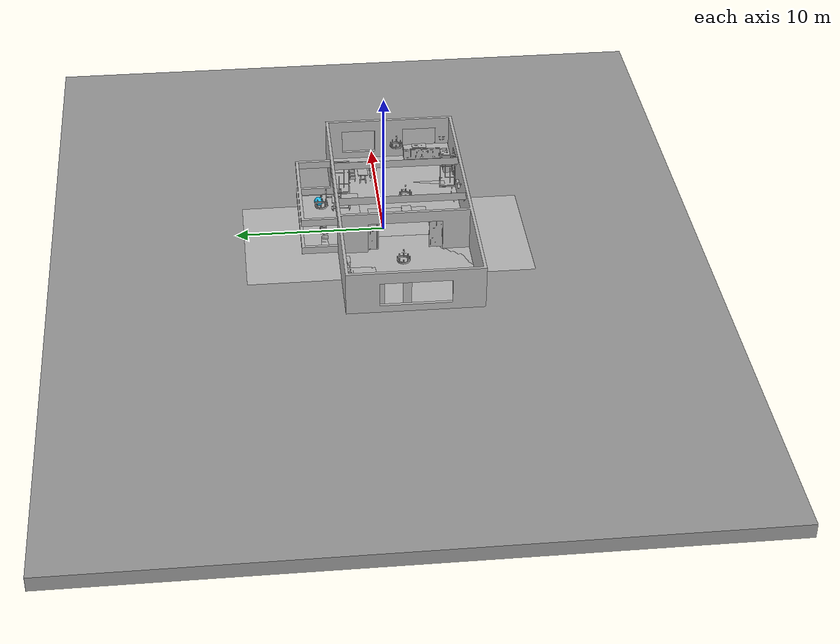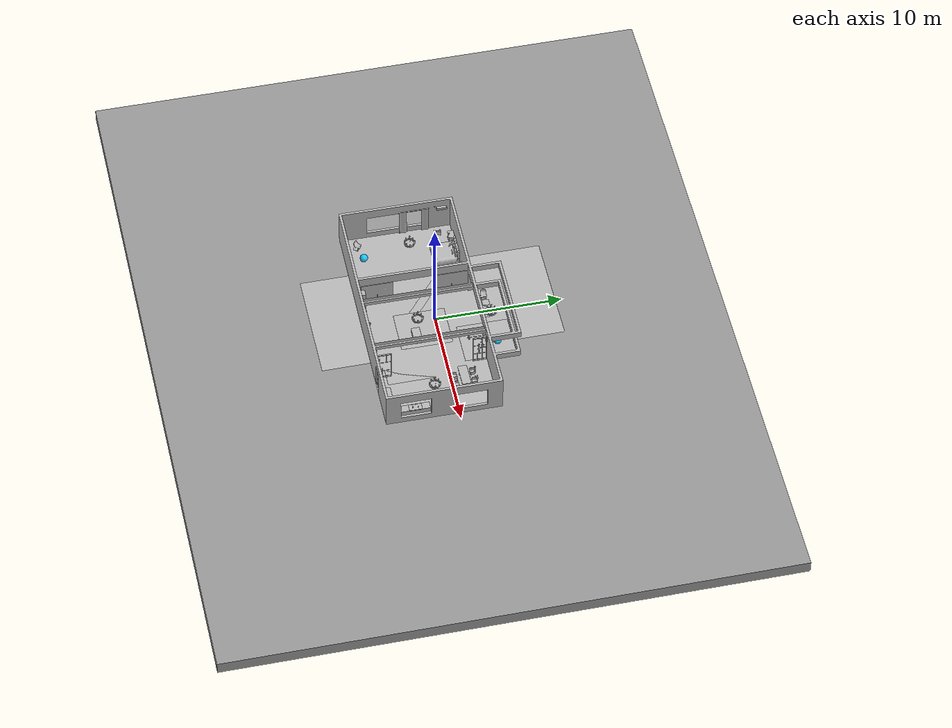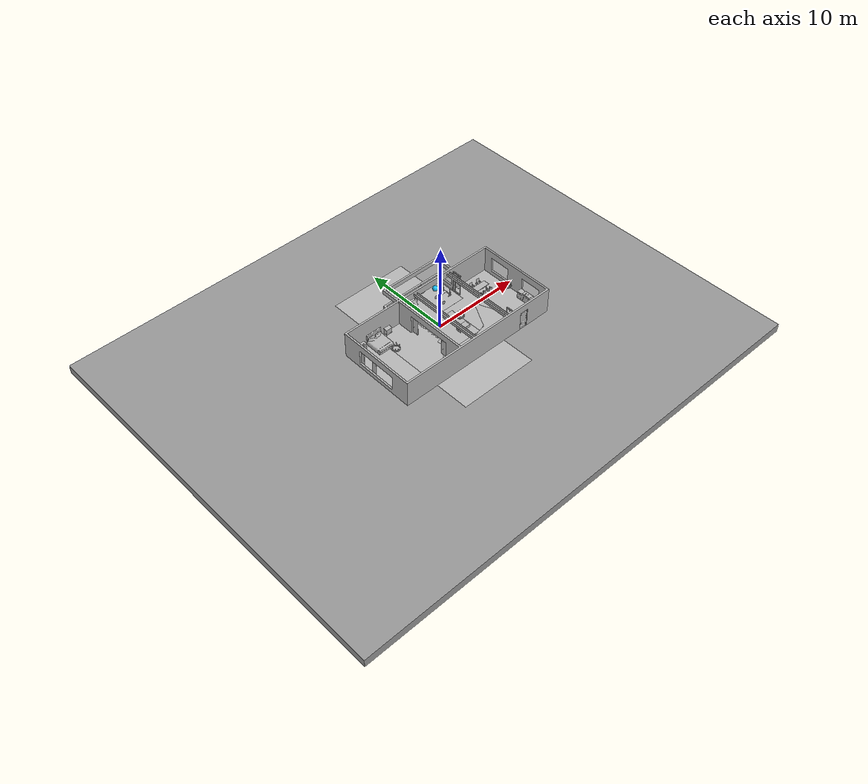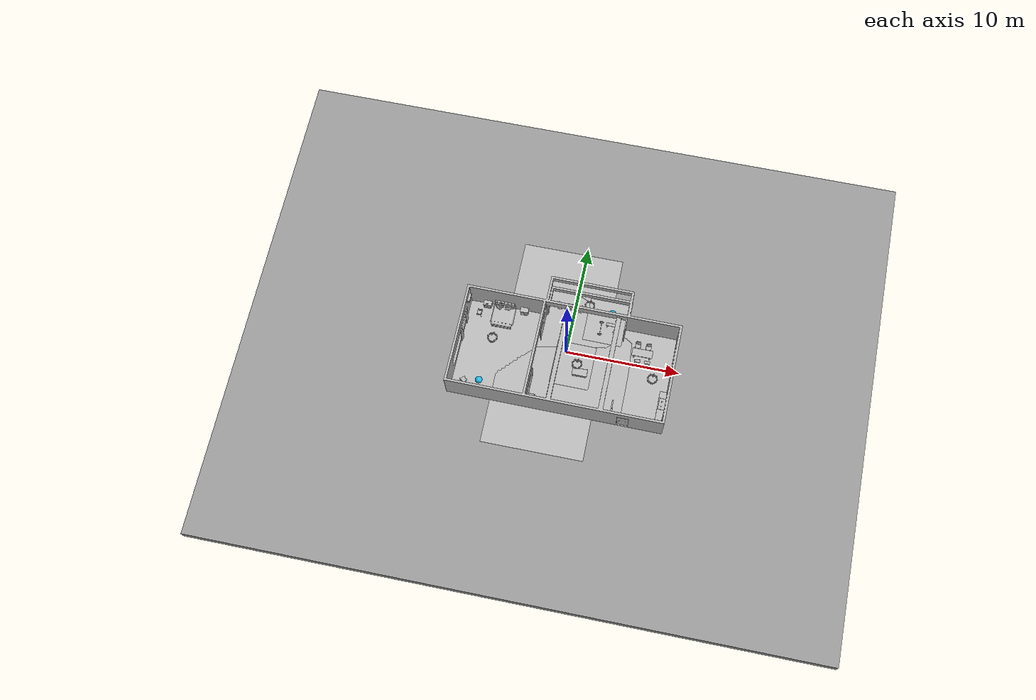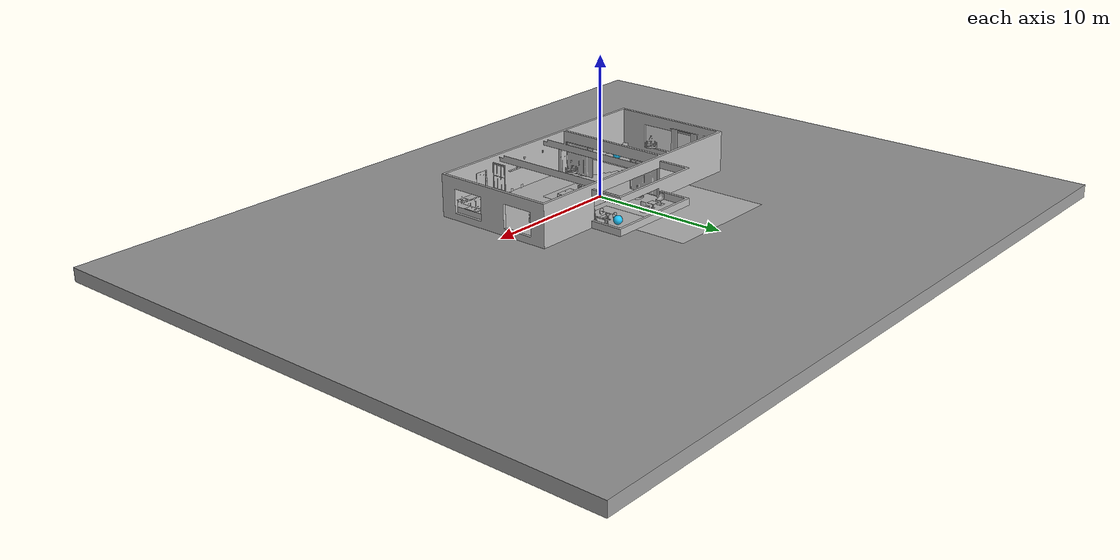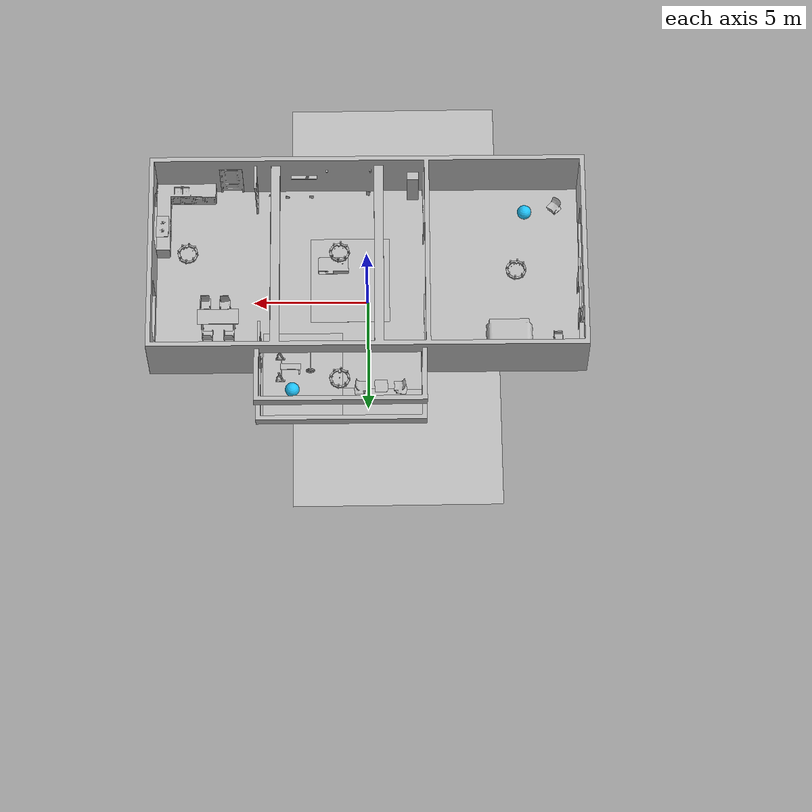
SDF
<sdf version="1.6">
 <world name="default">
  <gravity>0 0 -9.8</gravity>
  <magnetic_field>6e-06 2.3e-05 -4.2e-05</magnetic_field>
  <atmosphere type="adiabatic"/>
  <physics type="ode" name="rtu=1000,rtf=1,mss=0.001,iters=50" default="true">
   <real_time_update_rate>1000</real_time_update_rate>
   <real_time_factor>1</real_time_factor>
   <max_step_size>0.001</max_step_size>
   <ode><solver><type>quick</type><iters>50</iters></solver></ode>
  </physics>
  <physics type="ode" name="rtu=1000,rtf=1,mss=0.001,iters=25" default="false">
   <real_time_update_rate>1000</real_time_update_rate>
   <real_time_factor>1</real_time_factor>
   <max_step_size>0.001</max_step_size>
   <ode><solver><type>quick</type><iters>25</iters></solver></ode>
  </physics>
  <physics type="ode" name="rtu=1000,rtf=1,mss=0.001,iters=100" default="false">
   <real_time_update_rate>1000</real_time_update_rate>
   <real_time_factor>1</real_time_factor>
   <max_step_size>0.001</max_step_size>
   <ode><solver><type>quick</type><iters>100</iters></solver></ode>
  </physics>
  <physics type="ode" name="rtu=1000,rtf=1,mss=0.001,iters=200" default="false">
   <real_time_update_rate>1000</real_time_update_rate>
   <real_time_factor>1</real_time_factor>
   <max_step_size>0.001</max_step_size>
   <ode><solver><type>quick</type><iters>200</iters></solver></ode>
  </physics>
  <physics type="ode" name="rtu=1000,rtf=1,mss=0.0001,iters=50" default="false">
   <real_time_update_rate>1000</real_time_update_rate>
   <real_time_factor>1</real_time_factor>
   <max_step_size>0.0001</max_step_size>
   <ode><solver><type>quick</type><iters>50</iters></solver></ode>
  </physics>
  <physics type="ode" name="rtu=1000,rtf=1,mss=0.0001,iters=25" default="false">
   <real_time_update_rate>1000</real_time_update_rate>
   <real_time_factor>1</real_time_factor>
   <max_step_size>0.0001</max_step_size>
   <ode><solver><type>quick</type><iters>25</iters></solver></ode>
  </physics>
  <physics type="ode" name="rtu=1000,rtf=1,mss=0.0001,iters=100" default="false">
   <real_time_update_rate>1000</real_time_update_rate>
   <real_time_factor>1</real_time_factor>
   <max_step_size>0.0001</max_step_size>
   <ode><solver><type>quick</type><iters>100</iters></solver></ode>
  </physics>
  <physics type="ode" name="rtu=1000,rtf=1,mss=0.0001,iters=200" default="false">
   <real_time_update_rate>1000</real_time_update_rate>
   <real_time_factor>1</real_time_factor>
   <max_step_size>0.0001</max_step_size>
   <ode><solver><type>quick</type><iters>200</iters></solver></ode>
  </physics>
  <physics type="ode" name="rtu=1000,rtf=2,mss=0.001,iters=50" default="false">
   <real_time_update_rate>1000</real_time_update_rate>
   <real_time_factor>2</real_time_factor>
   <max_step_size>0.001</max_step_size>
   <ode><solver><type>quick</type><iters>50</iters></solver></ode>
  </physics>
  <physics type="ode" name="rtu=1000,rtf=2,mss=0.001,iters=25" default="false">
   <real_time_update_rate>1000</real_time_update_rate>
   <real_time_factor>2</real_time_factor>
   <max_step_size>0.001</max_step_size>
   <ode><solver><type>quick</type><iters>25</iters></solver></ode>
  </physics>
  <physics type="ode" name="rtu=1000,rtf=2,mss=0.001,iters=100" default="false">
   <real_time_update_rate>1000</real_time_update_rate>
   <real_time_factor>2</real_time_factor>
   <max_step_size>0.001</max_step_size>
   <ode><solver><type>quick</type><iters>100</iters></solver></ode>
  </physics>
  <physics type="ode" name="rtu=1000,rtf=2,mss=0.001,iters=200" default="false">
   <real_time_update_rate>1000</real_time_update_rate>
   <real_time_factor>2</real_time_factor>
   <max_step_size>0.001</max_step_size>
   <ode><solver><type>quick</type><iters>200</iters></solver></ode>
  </physics>
  <physics type="ode" name="rtu=1000,rtf=2,mss=0.0001,iters=50" default="false">
   <real_time_update_rate>1000</real_time_update_rate>
   <real_time_factor>2</real_time_factor>
   <max_step_size>0.0001</max_step_size>
   <ode><solver><type>quick</type><iters>50</iters></solver></ode>
  </physics>
  <physics type="ode" name="rtu=1000,rtf=2,mss=0.0001,iters=25" default="false">
   <real_time_update_rate>1000</real_time_update_rate>
   <real_time_factor>2</real_time_factor>
   <max_step_size>0.0001</max_step_size>
   <ode><solver><type>quick</type><iters>25</iters></solver></ode>
  </physics>
  <physics type="ode" name="rtu=1000,rtf=2,mss=0.0001,iters=100" default="false">
   <real_time_update_rate>1000</real_time_update_rate>
   <real_time_factor>2</real_time_factor>
   <max_step_size>0.0001</max_step_size>
   <ode><solver><type>quick</type><iters>100</iters></solver></ode>
  </physics>
  <physics type="ode" name="rtu=1000,rtf=2,mss=0.0001,iters=200" default="false">
   <real_time_update_rate>1000</real_time_update_rate>
   <real_time_factor>2</real_time_factor>
   <max_step_size>0.0001</max_step_size>
   <ode><solver><type>quick</type><iters>200</iters></solver></ode>
  </physics>
  <physics type="ode" name="rtu=1000,rtf=5,mss=0.001,iters=50" default="false">
   <real_time_update_rate>1000</real_time_update_rate>
   <real_time_factor>5</real_time_factor>
   <max_step_size>0.001</max_step_size>
   <ode><solver><type>quick</type><iters>50</iters></solver></ode>
  </physics>
  <physics type="ode" name="rtu=1000,rtf=5,mss=0.001,iters=25" default="false">
   <real_time_update_rate>1000</real_time_update_rate>
   <real_time_factor>5</real_time_factor>
   <max_step_size>0.001</max_step_size>
   <ode><solver><type>quick</type><iters>25</iters></solver></ode>
  </physics>
  <physics type="ode" name="rtu=1000,rtf=5,mss=0.001,iters=100" default="false">
   <real_time_update_rate>1000</real_time_update_rate>
   <real_time_factor>5</real_time_factor>
   <max_step_size>0.001</max_step_size>
   <ode><solver><type>quick</type><iters>100</iters></solver></ode>
  </physics>
  <physics type="ode" name="rtu=1000,rtf=5,mss=0.001,iters=200" default="false">
   <real_time_update_rate>1000</real_time_update_rate>
   <real_time_factor>5</real_time_factor>
   <max_step_size>0.001</max_step_size>
   <ode><solver><type>quick</type><iters>200</iters></solver></ode>
  </physics>
  <physics type="ode" name="rtu=1000,rtf=5,mss=0.0001,iters=50" default="false">
   <real_time_update_rate>1000</real_time_update_rate>
   <real_time_factor>5</real_time_factor>
   <max_step_size>0.0001</max_step_size>
   <ode><solver><type>quick</type><iters>50</iters></solver></ode>
  </physics>
  <physics type="ode" name="rtu=1000,rtf=5,mss=0.0001,iters=25" default="false">
   <real_time_update_rate>1000</real_time_update_rate>
   <real_time_factor>5</real_time_factor>
   <max_step_size>0.0001</max_step_size>
   <ode><solver><type>quick</type><iters>25</iters></solver></ode>
  </physics>
  <physics type="ode" name="rtu=1000,rtf=5,mss=0.0001,iters=100" default="false">
   <real_time_update_rate>1000</real_time_update_rate>
   <real_time_factor>5</real_time_factor>
   <max_step_size>0.0001</max_step_size>
   <ode><solver><type>quick</type><iters>100</iters></solver></ode>
  </physics>
  <physics type="ode" name="rtu=1000,rtf=5,mss=0.0001,iters=200" default="false">
   <real_time_update_rate>1000</real_time_update_rate>
   <real_time_factor>5</real_time_factor>
   <max_step_size>0.0001</max_step_size>
   <ode><solver><type>quick</type><iters>200</iters></solver></ode>
  </physics>
  <physics type="ode" name="rtu=1000,rtf=10,mss=0.001,iters=50" default="false">
   <real_time_update_rate>1000</real_time_update_rate>
   <real_time_factor>10</real_time_factor>
   <max_step_size>0.001</max_step_size>
   <ode><solver><type>quick</type><iters>50</iters></solver></ode>
  </physics>
  <physics type="ode" name="rtu=1000,rtf=10,mss=0.001,iters=25" default="false">
   <real_time_update_rate>1000</real_time_update_rate>
   <real_time_factor>10</real_time_factor>
   <max_step_size>0.001</max_step_size>
   <ode><solver><type>quick</type><iters>25</iters></solver></ode>
  </physics>
  <physics type="ode" name="rtu=1000,rtf=10,mss=0.001,iters=100" default="false">
   <real_time_update_rate>1000</real_time_update_rate>
   <real_time_factor>10</real_time_factor>
   <max_step_size>0.001</max_step_size>
   <ode><solver><type>quick</type><iters>100</iters></solver></ode>
  </physics>
  <physics type="ode" name="rtu=1000,rtf=10,mss=0.001,iters=200" default="false">
   <real_time_update_rate>1000</real_time_update_rate>
   <real_time_factor>10</real_time_factor>
   <max_step_size>0.001</max_step_size>
   <ode><solver><type>quick</type><iters>200</iters></solver></ode>
  </physics>
  <physics type="ode" name="rtu=1000,rtf=10,mss=0.0001,iters=50" default="false">
   <real_time_update_rate>1000</real_time_update_rate>
   <real_time_factor>10</real_time_factor>
   <max_step_size>0.0001</max_step_size>
   <ode><solver><type>quick</type><iters>50</iters></solver></ode>
  </physics>
  <physics type="ode" name="rtu=1000,rtf=10,mss=0.0001,iters=25" default="false">
   <real_time_update_rate>1000</real_time_update_rate>
   <real_time_factor>10</real_time_factor>
   <max_step_size>0.0001</max_step_size>
   <ode><solver><type>quick</type><iters>25</iters></solver></ode>
  </physics>
  <physics type="ode" name="rtu=1000,rtf=10,mss=0.0001,iters=100" default="false">
   <real_time_update_rate>1000</real_time_update_rate>
   <real_time_factor>10</real_time_factor>
   <max_step_size>0.0001</max_step_size>
   <ode><solver><type>quick</type><iters>100</iters></solver></ode>
  </physics>
  <physics type="ode" name="rtu=1000,rtf=10,mss=0.0001,iters=200" default="false">
   <real_time_update_rate>1000</real_time_update_rate>
   <real_time_factor>10</real_time_factor>
   <max_step_size>0.0001</max_step_size>
   <ode><solver><type>quick</type><iters>200</iters></solver></ode>
  </physics>
  <physics type="ode" name="rtu=1000,rtf=20,mss=0.001,iters=50" default="false">
   <real_time_update_rate>1000</real_time_update_rate>
   <real_time_factor>20</real_time_factor>
   <max_step_size>0.001</max_step_size>
   <ode><solver><type>quick</type><iters>50</iters></solver></ode>
  </physics>
  <physics type="ode" name="rtu=1000,rtf=20,mss=0.001,iters=25" default="false">
   <real_time_update_rate>1000</real_time_update_rate>
   <real_time_factor>20</real_time_factor>
   <max_step_size>0.001</max_step_size>
   <ode><solver><type>quick</type><iters>25</iters></solver></ode>
  </physics>
  <physics type="ode" name="rtu=1000,rtf=20,mss=0.001,iters=100" default="false">
   <real_time_update_rate>1000</real_time_update_rate>
   <real_time_factor>20</real_time_factor>
   <max_step_size>0.001</max_step_size>
   <ode><solver><type>quick</type><iters>100</iters></solver></ode>
  </physics>
  <physics type="ode" name="rtu=1000,rtf=20,mss=0.001,iters=200" default="false">
   <real_time_update_rate>1000</real_time_update_rate>
   <real_time_factor>20</real_time_factor>
   <max_step_size>0.001</max_step_size>
   <ode><solver><type>quick</type><iters>200</iters></solver></ode>
  </physics>
  <physics type="ode" name="rtu=1000,rtf=20,mss=0.0001,iters=50" default="false">
   <real_time_update_rate>1000</real_time_update_rate>
   <real_time_factor>20</real_time_factor>
   <max_step_size>0.0001</max_step_size>
   <ode><solver><type>quick</type><iters>50</iters></solver></ode>
  </physics>
  <physics type="ode" name="rtu=1000,rtf=20,mss=0.0001,iters=25" default="false">
   <real_time_update_rate>1000</real_time_update_rate>
   <real_time_factor>20</real_time_factor>
   <max_step_size>0.0001</max_step_size>
   <ode><solver><type>quick</type><iters>25</iters></solver></ode>
  </physics>
  <physics type="ode" name="rtu=1000,rtf=20,mss=0.0001,iters=100" default="false">
   <real_time_update_rate>1000</real_time_update_rate>
   <real_time_factor>20</real_time_factor>
   <max_step_size>0.0001</max_step_size>
   <ode><solver><type>quick</type><iters>100</iters></solver></ode>
  </physics>
  <physics type="ode" name="rtu=1000,rtf=20,mss=0.0001,iters=200" default="false">
   <real_time_update_rate>1000</real_time_update_rate>
   <real_time_factor>20</real_time_factor>
   <max_step_size>0.0001</max_step_size>
   <ode><solver><type>quick</type><iters>200</iters></solver></ode>
  </physics>
  <physics type="ode" name="rtu=2000,rtf=1,mss=0.001,iters=50" default="false">
   <real_time_update_rate>2000</real_time_update_rate>
   <real_time_factor>1</real_time_factor>
   <max_step_size>0.001</max_step_size>
   <ode><solver><type>quick</type><iters>50</iters></solver></ode>
  </physics>
  <physics type="ode" name="rtu=2000,rtf=1,mss=0.001,iters=25" default="false">
   <real_time_update_rate>2000</real_time_update_rate>
   <real_time_factor>1</real_time_factor>
   <max_step_size>0.001</max_step_size>
   <ode><solver><type>quick</type><iters>25</iters></solver></ode>
  </physics>
  <physics type="ode" name="rtu=2000,rtf=1,mss=0.001,iters=100" default="false">
   <real_time_update_rate>2000</real_time_update_rate>
   <real_time_factor>1</real_time_factor>
   <max_step_size>0.001</max_step_size>
   <ode><solver><type>quick</type><iters>100</iters></solver></ode>
  </physics>
  <physics type="ode" name="rtu=2000,rtf=1,mss=0.001,iters=200" default="false">
   <real_time_update_rate>2000</real_time_update_rate>
   <real_time_factor>1</real_time_factor>
   <max_step_size>0.001</max_step_size>
   <ode><solver><type>quick</type><iters>200</iters></solver></ode>
  </physics>
  <physics type="ode" name="rtu=2000,rtf=1,mss=0.0001,iters=50" default="false">
   <real_time_update_rate>2000</real_time_update_rate>
   <real_time_factor>1</real_time_factor>
   <max_step_size>0.0001</max_step_size>
   <ode><solver><type>quick</type><iters>50</iters></solver></ode>
  </physics>
  <physics type="ode" name="rtu=2000,rtf=1,mss=0.0001,iters=25" default="false">
   <real_time_update_rate>2000</real_time_update_rate>
   <real_time_factor>1</real_time_factor>
   <max_step_size>0.0001</max_step_size>
   <ode><solver><type>quick</type><iters>25</iters></solver></ode>
  </physics>
  <physics type="ode" name="rtu=2000,rtf=1,mss=0.0001,iters=100" default="false">
   <real_time_update_rate>2000</real_time_update_rate>
   <real_time_factor>1</real_time_factor>
   <max_step_size>0.0001</max_step_size>
   <ode><solver><type>quick</type><iters>100</iters></solver></ode>
  </physics>
  <physics type="ode" name="rtu=2000,rtf=1,mss=0.0001,iters=200" default="false">
   <real_time_update_rate>2000</real_time_update_rate>
   <real_time_factor>1</real_time_factor>
   <max_step_size>0.0001</max_step_size>
   <ode><solver><type>quick</type><iters>200</iters></solver></ode>
  </physics>
  <physics type="ode" name="rtu=2000,rtf=2,mss=0.001,iters=50" default="false">
   <real_time_update_rate>2000</real_time_update_rate>
   <real_time_factor>2</real_time_factor>
   <max_step_size>0.001</max_step_size>
   <ode><solver><type>quick</type><iters>50</iters></solver></ode>
  </physics>
  <physics type="ode" name="rtu=2000,rtf=2,mss=0.001,iters=25" default="false">
   <real_time_update_rate>2000</real_time_update_rate>
   <real_time_factor>2</real_time_factor>
   <max_step_size>0.001</max_step_size>
   <ode><solver><type>quick</type><iters>25</iters></solver></ode>
  </physics>
  <physics type="ode" name="rtu=2000,rtf=2,mss=0.001,iters=100" default="false">
   <real_time_update_rate>2000</real_time_update_rate>
   <real_time_factor>2</real_time_factor>
   <max_step_size>0.001</max_step_size>
   <ode><solver><type>quick</type><iters>100</iters></solver></ode>
  </physics>
  <physics type="ode" name="rtu=2000,rtf=2,mss=0.001,iters=200" default="false">
   <real_time_update_rate>2000</real_time_update_rate>
   <real_time_factor>2</real_time_factor>
   <max_step_size>0.001</max_step_size>
   <ode><solver><type>quick</type><iters>200</iters></solver></ode>
  </physics>
  <physics type="ode" name="rtu=2000,rtf=2,mss=0.0001,iters=50" default="false">
   <real_time_update_rate>2000</real_time_update_rate>
   <real_time_factor>2</real_time_factor>
   <max_step_size>0.0001</max_step_size>
   <ode><solver><type>quick</type><iters>50</iters></solver></ode>
  </physics>
  <physics type="ode" name="rtu=2000,rtf=2,mss=0.0001,iters=25" default="false">
   <real_time_update_rate>2000</real_time_update_rate>
   <real_time_factor>2</real_time_factor>
   <max_step_size>0.0001</max_step_size>
   <ode><solver><type>quick</type><iters>25</iters></solver></ode>
  </physics>
  <physics type="ode" name="rtu=2000,rtf=2,mss=0.0001,iters=100" default="false">
   <real_time_update_rate>2000</real_time_update_rate>
   <real_time_factor>2</real_time_factor>
   <max_step_size>0.0001</max_step_size>
   <ode><solver><type>quick</type><iters>100</iters></solver></ode>
  </physics>
  <physics type="ode" name="rtu=2000,rtf=2,mss=0.0001,iters=200" default="false">
   <real_time_update_rate>2000</real_time_update_rate>
   <real_time_factor>2</real_time_factor>
   <max_step_size>0.0001</max_step_size>
   <ode><solver><type>quick</type><iters>200</iters></solver></ode>
  </physics>
  <physics type="ode" name="rtu=2000,rtf=5,mss=0.001,iters=50" default="false">
   <real_time_update_rate>2000</real_time_update_rate>
   <real_time_factor>5</real_time_factor>
   <max_step_size>0.001</max_step_size>
   <ode><solver><type>quick</type><iters>50</iters></solver></ode>
  </physics>
  <physics type="ode" name="rtu=2000,rtf=5,mss=0.001,iters=25" default="false">
   <real_time_update_rate>2000</real_time_update_rate>
   <real_time_factor>5</real_time_factor>
   <max_step_size>0.001</max_step_size>
   <ode><solver><type>quick</type><iters>25</iters></solver></ode>
  </physics>
  <physics type="ode" name="rtu=2000,rtf=5,mss=0.001,iters=100" default="false">
   <real_time_update_rate>2000</real_time_update_rate>
   <real_time_factor>5</real_time_factor>
   <max_step_size>0.001</max_step_size>
   <ode><solver><type>quick</type><iters>100</iters></solver></ode>
  </physics>
  <physics type="ode" name="rtu=2000,rtf=5,mss=0.001,iters=200" default="false">
   <real_time_update_rate>2000</real_time_update_rate>
   <real_time_factor>5</real_time_factor>
   <max_step_size>0.001</max_step_size>
   <ode><solver><type>quick</type><iters>200</iters></solver></ode>
  </physics>
  <physics type="ode" name="rtu=2000,rtf=5,mss=0.0001,iters=50" default="false">
   <real_time_update_rate>2000</real_time_update_rate>
   <real_time_factor>5</real_time_factor>
   <max_step_size>0.0001</max_step_size>
   <ode><solver><type>quick</type><iters>50</iters></solver></ode>
  </physics>
  <physics type="ode" name="rtu=2000,rtf=5,mss=0.0001,iters=25" default="false">
   <real_time_update_rate>2000</real_time_update_rate>
   <real_time_factor>5</real_time_factor>
   <max_step_size>0.0001</max_step_size>
   <ode><solver><type>quick</type><iters>25</iters></solver></ode>
  </physics>
  <physics type="ode" name="rtu=2000,rtf=5,mss=0.0001,iters=100" default="false">
   <real_time_update_rate>2000</real_time_update_rate>
   <real_time_factor>5</real_time_factor>
   <max_step_size>0.0001</max_step_size>
   <ode><solver><type>quick</type><iters>100</iters></solver></ode>
  </physics>
  <physics type="ode" name="rtu=2000,rtf=5,mss=0.0001,iters=200" default="false">
   <real_time_update_rate>2000</real_time_update_rate>
   <real_time_factor>5</real_time_factor>
   <max_step_size>0.0001</max_step_size>
   <ode><solver><type>quick</type><iters>200</iters></solver></ode>
  </physics>
  <physics type="ode" name="rtu=2000,rtf=10,mss=0.001,iters=50" default="false">
   <real_time_update_rate>2000</real_time_update_rate>
   <real_time_factor>10</real_time_factor>
   <max_step_size>0.001</max_step_size>
   <ode><solver><type>quick</type><iters>50</iters></solver></ode>
  </physics>
  <physics type="ode" name="rtu=2000,rtf=10,mss=0.001,iters=25" default="false">
   <real_time_update_rate>2000</real_time_update_rate>
   <real_time_factor>10</real_time_factor>
   <max_step_size>0.001</max_step_size>
   <ode><solver><type>quick</type><iters>25</iters></solver></ode>
  </physics>
  <physics type="ode" name="rtu=2000,rtf=10,mss=0.001,iters=100" default="false">
   <real_time_update_rate>2000</real_time_update_rate>
   <real_time_factor>10</real_time_factor>
   <max_step_size>0.001</max_step_size>
   <ode><solver><type>quick</type><iters>100</iters></solver></ode>
  </physics>
  <physics type="ode" name="rtu=2000,rtf=10,mss=0.001,iters=200" default="false">
   <real_time_update_rate>2000</real_time_update_rate>
   <real_time_factor>10</real_time_factor>
   <max_step_size>0.001</max_step_size>
   <ode><solver><type>quick</type><iters>200</iters></solver></ode>
  </physics>
  <physics type="ode" name="rtu=2000,rtf=10,mss=0.0001,iters=50" default="false">
   <real_time_update_rate>2000</real_time_update_rate>
   <real_time_factor>10</real_time_factor>
   <max_step_size>0.0001</max_step_size>
   <ode><solver><type>quick</type><iters>50</iters></solver></ode>
  </physics>
  <physics type="ode" name="rtu=2000,rtf=10,mss=0.0001,iters=25" default="false">
   <real_time_update_rate>2000</real_time_update_rate>
   <real_time_factor>10</real_time_factor>
   <max_step_size>0.0001</max_step_size>
   <ode><solver><type>quick</type><iters>25</iters></solver></ode>
  </physics>
  <physics type="ode" name="rtu=2000,rtf=10,mss=0.0001,iters=100" default="false">
   <real_time_update_rate>2000</real_time_update_rate>
   <real_time_factor>10</real_time_factor>
   <max_step_size>0.0001</max_step_size>
   <ode><solver><type>quick</type><iters>100</iters></solver></ode>
  </physics>
  <physics type="ode" name="rtu=2000,rtf=10,mss=0.0001,iters=200" default="false">
   <real_time_update_rate>2000</real_time_update_rate>
   <real_time_factor>10</real_time_factor>
   <max_step_size>0.0001</max_step_size>
   <ode><solver><type>quick</type><iters>200</iters></solver></ode>
  </physics>
  <physics type="ode" name="rtu=2000,rtf=20,mss=0.001,iters=50" default="false">
   <real_time_update_rate>2000</real_time_update_rate>
   <real_time_factor>20</real_time_factor>
   <max_step_size>0.001</max_step_size>
   <ode><solver><type>quick</type><iters>50</iters></solver></ode>
  </physics>
  <physics type="ode" name="rtu=2000,rtf=20,mss=0.001,iters=25" default="false">
   <real_time_update_rate>2000</real_time_update_rate>
   <real_time_factor>20</real_time_factor>
   <max_step_size>0.001</max_step_size>
   <ode><solver><type>quick</type><iters>25</iters></solver></ode>
  </physics>
  <physics type="ode" name="rtu=2000,rtf=20,mss=0.001,iters=100" default="false">
   <real_time_update_rate>2000</real_time_update_rate>
   <real_time_factor>20</real_time_factor>
   <max_step_size>0.001</max_step_size>
   <ode><solver><type>quick</type><iters>100</iters></solver></ode>
  </physics>
  <physics type="ode" name="rtu=2000,rtf=20,mss=0.001,iters=200" default="false">
   <real_time_update_rate>2000</real_time_update_rate>
   <real_time_factor>20</real_time_factor>
   <max_step_size>0.001</max_step_size>
   <ode><solver><type>quick</type><iters>200</iters></solver></ode>
  </physics>
  <physics type="ode" name="rtu=2000,rtf=20,mss=0.0001,iters=50" default="false">
   <real_time_update_rate>2000</real_time_update_rate>
   <real_time_factor>20</real_time_factor>
   <max_step_size>0.0001</max_step_size>
   <ode><solver><type>quick</type><iters>50</iters></solver></ode>
  </physics>
  <physics type="ode" name="rtu=2000,rtf=20,mss=0.0001,iters=25" default="false">
   <real_time_update_rate>2000</real_time_update_rate>
   <real_time_factor>20</real_time_factor>
   <max_step_size>0.0001</max_step_size>
   <ode><solver><type>quick</type><iters>25</iters></solver></ode>
  </physics>
  <physics type="ode" name="rtu=2000,rtf=20,mss=0.0001,iters=100" default="false">
   <real_time_update_rate>2000</real_time_update_rate>
   <real_time_factor>20</real_time_factor>
   <max_step_size>0.0001</max_step_size>
   <ode><solver><type>quick</type><iters>100</iters></solver></ode>
  </physics>
  <physics type="ode" name="rtu=2000,rtf=20,mss=0.0001,iters=200" default="false">
   <real_time_update_rate>2000</real_time_update_rate>
   <real_time_factor>20</real_time_factor>
   <max_step_size>0.0001</max_step_size>
   <ode><solver><type>quick</type><iters>200</iters></solver></ode>
  </physics>
  <physics type="ode" name="rtu=5000,rtf=1,mss=0.001,iters=50" default="false">
   <real_time_update_rate>5000</real_time_update_rate>
   <real_time_factor>1</real_time_factor>
   <max_step_size>0.001</max_step_size>
   <ode><solver><type>quick</type><iters>50</iters></solver></ode>
  </physics>
  <physics type="ode" name="rtu=5000,rtf=1,mss=0.001,iters=25" default="false">
   <real_time_update_rate>5000</real_time_update_rate>
   <real_time_factor>1</real_time_factor>
   <max_step_size>0.001</max_step_size>
   <ode><solver><type>quick</type><iters>25</iters></solver></ode>
  </physics>
  <physics type="ode" name="rtu=5000,rtf=1,mss=0.001,iters=100" default="false">
   <real_time_update_rate>5000</real_time_update_rate>
   <real_time_factor>1</real_time_factor>
   <max_step_size>0.001</max_step_size>
   <ode><solver><type>quick</type><iters>100</iters></solver></ode>
  </physics>
  <physics type="ode" name="rtu=5000,rtf=1,mss=0.001,iters=200" default="false">
   <real_time_update_rate>5000</real_time_update_rate>
   <real_time_factor>1</real_time_factor>
   <max_step_size>0.001</max_step_size>
   <ode><solver><type>quick</type><iters>200</iters></solver></ode>
  </physics>
  <physics type="ode" name="rtu=5000,rtf=1,mss=0.0001,iters=50" default="false">
   <real_time_update_rate>5000</real_time_update_rate>
   <real_time_factor>1</real_time_factor>
   <max_step_size>0.0001</max_step_size>
   <ode><solver><type>quick</type><iters>50</iters></solver></ode>
  </physics>
  <physics type="ode" name="rtu=5000,rtf=1,mss=0.0001,iters=25" default="false">
   <real_time_update_rate>5000</real_time_update_rate>
   <real_time_factor>1</real_time_factor>
   <max_step_size>0.0001</max_step_size>
   <ode><solver><type>quick</type><iters>25</iters></solver></ode>
  </physics>
  <physics type="ode" name="rtu=5000,rtf=1,mss=0.0001,iters=100" default="false">
   <real_time_update_rate>5000</real_time_update_rate>
   <real_time_factor>1</real_time_factor>
   <max_step_size>0.0001</max_step_size>
   <ode><solver><type>quick</type><iters>100</iters></solver></ode>
  </physics>
  <physics type="ode" name="rtu=5000,rtf=1,mss=0.0001,iters=200" default="false">
   <real_time_update_rate>5000</real_time_update_rate>
   <real_time_factor>1</real_time_factor>
   <max_step_size>0.0001</max_step_size>
   <ode><solver><type>quick</type><iters>200</iters></solver></ode>
  </physics>
  <physics type="ode" name="rtu=5000,rtf=2,mss=0.001,iters=50" default="false">
   <real_time_update_rate>5000</real_time_update_rate>
   <real_time_factor>2</real_time_factor>
   <max_step_size>0.001</max_step_size>
   <ode><solver><type>quick</type><iters>50</iters></solver></ode>
  </physics>
  <physics type="ode" name="rtu=5000,rtf=2,mss=0.001,iters=25" default="false">
   <real_time_update_rate>5000</real_time_update_rate>
   <real_time_factor>2</real_time_factor>
   <max_step_size>0.001</max_step_size>
   <ode><solver><type>quick</type><iters>25</iters></solver></ode>
  </physics>
  <physics type="ode" name="rtu=5000,rtf=2,mss=0.001,iters=100" default="false">
   <real_time_update_rate>5000</real_time_update_rate>
   <real_time_factor>2</real_time_factor>
   <max_step_size>0.001</max_step_size>
   <ode><solver><type>quick</type><iters>100</iters></solver></ode>
  </physics>
  <physics type="ode" name="rtu=5000,rtf=2,mss=0.001,iters=200" default="false">
   <real_time_update_rate>5000</real_time_update_rate>
   <real_time_factor>2</real_time_factor>
   <max_step_size>0.001</max_step_size>
   <ode><solver><type>quick</type><iters>200</iters></solver></ode>
  </physics>
  <physics type="ode" name="rtu=5000,rtf=2,mss=0.0001,iters=50" default="false">
   <real_time_update_rate>5000</real_time_update_rate>
   <real_time_factor>2</real_time_factor>
   <max_step_size>0.0001</max_step_size>
   <ode><solver><type>quick</type><iters>50</iters></solver></ode>
  </physics>
  <physics type="ode" name="rtu=5000,rtf=2,mss=0.0001,iters=25" default="false">
   <real_time_update_rate>5000</real_time_update_rate>
   <real_time_factor>2</real_time_factor>
   <max_step_size>0.0001</max_step_size>
   <ode><solver><type>quick</type><iters>25</iters></solver></ode>
  </physics>
  <physics type="ode" name="rtu=5000,rtf=2,mss=0.0001,iters=100" default="false">
   <real_time_update_rate>5000</real_time_update_rate>
   <real_time_factor>2</real_time_factor>
   <max_step_size>0.0001</max_step_size>
   <ode><solver><type>quick</type><iters>100</iters></solver></ode>
  </physics>
  <physics type="ode" name="rtu=5000,rtf=2,mss=0.0001,iters=200" default="false">
   <real_time_update_rate>5000</real_time_update_rate>
   <real_time_factor>2</real_time_factor>
   <max_step_size>0.0001</max_step_size>
   <ode><solver><type>quick</type><iters>200</iters></solver></ode>
  </physics>
  <physics type="ode" name="rtu=5000,rtf=5,mss=0.001,iters=50" default="false">
   <real_time_update_rate>5000</real_time_update_rate>
   <real_time_factor>5</real_time_factor>
   <max_step_size>0.001</max_step_size>
   <ode><solver><type>quick</type><iters>50</iters></solver></ode>
  </physics>
  <physics type="ode" name="rtu=5000,rtf=5,mss=0.001,iters=25" default="false">
   <real_time_update_rate>5000</real_time_update_rate>
   <real_time_factor>5</real_time_factor>
   <max_step_size>0.001</max_step_size>
   <ode><solver><type>quick</type><iters>25</iters></solver></ode>
  </physics>
  <physics type="ode" name="rtu=5000,rtf=5,mss=0.001,iters=100" default="false">
   <real_time_update_rate>5000</real_time_update_rate>
   <real_time_factor>5</real_time_factor>
   <max_step_size>0.001</max_step_size>
   <ode><solver><type>quick</type><iters>100</iters></solver></ode>
  </physics>
  <physics type="ode" name="rtu=5000,rtf=5,mss=0.001,iters=200" default="false">
   <real_time_update_rate>5000</real_time_update_rate>
   <real_time_factor>5</real_time_factor>
   <max_step_size>0.001</max_step_size>
   <ode><solver><type>quick</type><iters>200</iters></solver></ode>
  </physics>
  <physics type="ode" name="rtu=5000,rtf=5,mss=0.0001,iters=50" default="false">
   <real_time_update_rate>5000</real_time_update_rate>
   <real_time_factor>5</real_time_factor>
   <max_step_size>0.0001</max_step_size>
   <ode><solver><type>quick</type><iters>50</iters></solver></ode>
  </physics>
  <physics type="ode" name="rtu=5000,rtf=5,mss=0.0001,iters=25" default="false">
   <real_time_update_rate>5000</real_time_update_rate>
   <real_time_factor>5</real_time_factor>
   <max_step_size>0.0001</max_step_size>
   <ode><solver><type>quick</type><iters>25</iters></solver></ode>
  </physics>
  <physics type="ode" name="rtu=5000,rtf=5,mss=0.0001,iters=100" default="false">
   <real_time_update_rate>5000</real_time_update_rate>
   <real_time_factor>5</real_time_factor>
   <max_step_size>0.0001</max_step_size>
   <ode><solver><type>quick</type><iters>100</iters></solver></ode>
  </physics>
  <physics type="ode" name="rtu=5000,rtf=5,mss=0.0001,iters=200" default="false">
   <real_time_update_rate>5000</real_time_update_rate>
   <real_time_factor>5</real_time_factor>
   <max_step_size>0.0001</max_step_size>
   <ode><solver><type>quick</type><iters>200</iters></solver></ode>
  </physics>
  <physics type="ode" name="rtu=5000,rtf=10,mss=0.001,iters=50" default="false">
   <real_time_update_rate>5000</real_time_update_rate>
   <real_time_factor>10</real_time_factor>
   <max_step_size>0.001</max_step_size>
   <ode><solver><type>quick</type><iters>50</iters></solver></ode>
  </physics>
  <physics type="ode" name="rtu=5000,rtf=10,mss=0.001,iters=25" default="false">
   <real_time_update_rate>5000</real_time_update_rate>
   <real_time_factor>10</real_time_factor>
   <max_step_size>0.001</max_step_size>
   <ode><solver><type>quick</type><iters>25</iters></solver></ode>
  </physics>
  <physics type="ode" name="rtu=5000,rtf=10,mss=0.001,iters=100" default="false">
   <real_time_update_rate>5000</real_time_update_rate>
   <real_time_factor>10</real_time_factor>
   <max_step_size>0.001</max_step_size>
   <ode><solver><type>quick</type><iters>100</iters></solver></ode>
  </physics>
  <physics type="ode" name="rtu=5000,rtf=10,mss=0.001,iters=200" default="false">
   <real_time_update_rate>5000</real_time_update_rate>
   <real_time_factor>10</real_time_factor>
   <max_step_size>0.001</max_step_size>
   <ode><solver><type>quick</type><iters>200</iters></solver></ode>
  </physics>
  <physics type="ode" name="rtu=5000,rtf=10,mss=0.0001,iters=50" default="false">
   <real_time_update_rate>5000</real_time_update_rate>
   <real_time_factor>10</real_time_factor>
   <max_step_size>0.0001</max_step_size>
   <ode><solver><type>quick</type><iters>50</iters></solver></ode>
  </physics>
  <physics type="ode" name="rtu=5000,rtf=10,mss=0.0001,iters=25" default="false">
   <real_time_update_rate>5000</real_time_update_rate>
   <real_time_factor>10</real_time_factor>
   <max_step_size>0.0001</max_step_size>
   <ode><solver><type>quick</type><iters>25</iters></solver></ode>
  </physics>
  <physics type="ode" name="rtu=5000,rtf=10,mss=0.0001,iters=100" default="false">
   <real_time_update_rate>5000</real_time_update_rate>
   <real_time_factor>10</real_time_factor>
   <max_step_size>0.0001</max_step_size>
   <ode><solver><type>quick</type><iters>100</iters></solver></ode>
  </physics>
  <physics type="ode" name="rtu=5000,rtf=10,mss=0.0001,iters=200" default="false">
   <real_time_update_rate>5000</real_time_update_rate>
   <real_time_factor>10</real_time_factor>
   <max_step_size>0.0001</max_step_size>
   <ode><solver><type>quick</type><iters>200</iters></solver></ode>
  </physics>
  <physics type="ode" name="rtu=5000,rtf=20,mss=0.001,iters=50" default="false">
   <real_time_update_rate>5000</real_time_update_rate>
   <real_time_factor>20</real_time_factor>
   <max_step_size>0.001</max_step_size>
   <ode><solver><type>quick</type><iters>50</iters></solver></ode>
  </physics>
  <physics type="ode" name="rtu=5000,rtf=20,mss=0.001,iters=25" default="false">
   <real_time_update_rate>5000</real_time_update_rate>
   <real_time_factor>20</real_time_factor>
   <max_step_size>0.001</max_step_size>
   <ode><solver><type>quick</type><iters>25</iters></solver></ode>
  </physics>
  <physics type="ode" name="rtu=5000,rtf=20,mss=0.001,iters=100" default="false">
   <real_time_update_rate>5000</real_time_update_rate>
   <real_time_factor>20</real_time_factor>
   <max_step_size>0.001</max_step_size>
   <ode><solver><type>quick</type><iters>100</iters></solver></ode>
  </physics>
  <physics type="ode" name="rtu=5000,rtf=20,mss=0.001,iters=200" default="false">
   <real_time_update_rate>5000</real_time_update_rate>
   <real_time_factor>20</real_time_factor>
   <max_step_size>0.001</max_step_size>
   <ode><solver><type>quick</type><iters>200</iters></solver></ode>
  </physics>
  <physics type="ode" name="rtu=5000,rtf=20,mss=0.0001,iters=50" default="false">
   <real_time_update_rate>5000</real_time_update_rate>
   <real_time_factor>20</real_time_factor>
   <max_step_size>0.0001</max_step_size>
   <ode><solver><type>quick</type><iters>50</iters></solver></ode>
  </physics>
  <physics type="ode" name="rtu=5000,rtf=20,mss=0.0001,iters=25" default="false">
   <real_time_update_rate>5000</real_time_update_rate>
   <real_time_factor>20</real_time_factor>
   <max_step_size>0.0001</max_step_size>
   <ode><solver><type>quick</type><iters>25</iters></solver></ode>
  </physics>
  <physics type="ode" name="rtu=5000,rtf=20,mss=0.0001,iters=100" default="false">
   <real_time_update_rate>5000</real_time_update_rate>
   <real_time_factor>20</real_time_factor>
   <max_step_size>0.0001</max_step_size>
   <ode><solver><type>quick</type><iters>100</iters></solver></ode>
  </physics>
  <physics type="ode" name="rtu=5000,rtf=20,mss=0.0001,iters=200" default="false">
   <real_time_update_rate>5000</real_time_update_rate>
   <real_time_factor>20</real_time_factor>
   <max_step_size>0.0001</max_step_size>
   <ode><solver><type>quick</type><iters>200</iters></solver></ode>
  </physics>
  <physics type="ode" name="rtu=10000,rtf=1,mss=0.001,iters=50" default="false">
   <real_time_update_rate>10000</real_time_update_rate>
   <real_time_factor>1</real_time_factor>
   <max_step_size>0.001</max_step_size>
   <ode><solver><type>quick</type><iters>50</iters></solver></ode>
  </physics>
  <physics type="ode" name="rtu=10000,rtf=1,mss=0.001,iters=25" default="false">
   <real_time_update_rate>10000</real_time_update_rate>
   <real_time_factor>1</real_time_factor>
   <max_step_size>0.001</max_step_size>
   <ode><solver><type>quick</type><iters>25</iters></solver></ode>
  </physics>
  <physics type="ode" name="rtu=10000,rtf=1,mss=0.001,iters=100" default="false">
   <real_time_update_rate>10000</real_time_update_rate>
   <real_time_factor>1</real_time_factor>
   <max_step_size>0.001</max_step_size>
   <ode><solver><type>quick</type><iters>100</iters></solver></ode>
  </physics>
  <physics type="ode" name="rtu=10000,rtf=1,mss=0.001,iters=200" default="false">
   <real_time_update_rate>10000</real_time_update_rate>
   <real_time_factor>1</real_time_factor>
   <max_step_size>0.001</max_step_size>
   <ode><solver><type>quick</type><iters>200</iters></solver></ode>
  </physics>
  <physics type="ode" name="rtu=10000,rtf=1,mss=0.0001,iters=50" default="false">
   <real_time_update_rate>10000</real_time_update_rate>
   <real_time_factor>1</real_time_factor>
   <max_step_size>0.0001</max_step_size>
   <ode><solver><type>quick</type><iters>50</iters></solver></ode>
  </physics>
  <physics type="ode" name="rtu=10000,rtf=1,mss=0.0001,iters=25" default="false">
   <real_time_update_rate>10000</real_time_update_rate>
   <real_time_factor>1</real_time_factor>
   <max_step_size>0.0001</max_step_size>
   <ode><solver><type>quick</type><iters>25</iters></solver></ode>
  </physics>
  <physics type="ode" name="rtu=10000,rtf=1,mss=0.0001,iters=100" default="false">
   <real_time_update_rate>10000</real_time_update_rate>
   <real_time_factor>1</real_time_factor>
   <max_step_size>0.0001</max_step_size>
   <ode><solver><type>quick</type><iters>100</iters></solver></ode>
  </physics>
  <physics type="ode" name="rtu=10000,rtf=1,mss=0.0001,iters=200" default="false">
   <real_time_update_rate>10000</real_time_update_rate>
   <real_time_factor>1</real_time_factor>
   <max_step_size>0.0001</max_step_size>
   <ode><solver><type>quick</type><iters>200</iters></solver></ode>
  </physics>
  <physics type="ode" name="rtu=10000,rtf=2,mss=0.001,iters=50" default="false">
   <real_time_update_rate>10000</real_time_update_rate>
   <real_time_factor>2</real_time_factor>
   <max_step_size>0.001</max_step_size>
   <ode><solver><type>quick</type><iters>50</iters></solver></ode>
  </physics>
  <physics type="ode" name="rtu=10000,rtf=2,mss=0.001,iters=25" default="false">
   <real_time_update_rate>10000</real_time_update_rate>
   <real_time_factor>2</real_time_factor>
   <max_step_size>0.001</max_step_size>
   <ode><solver><type>quick</type><iters>25</iters></solver></ode>
  </physics>
  <physics type="ode" name="rtu=10000,rtf=2,mss=0.001,iters=100" default="false">
   <real_time_update_rate>10000</real_time_update_rate>
   <real_time_factor>2</real_time_factor>
   <max_step_size>0.001</max_step_size>
   <ode><solver><type>quick</type><iters>100</iters></solver></ode>
  </physics>
  <physics type="ode" name="rtu=10000,rtf=2,mss=0.001,iters=200" default="false">
   <real_time_update_rate>10000</real_time_update_rate>
   <real_time_factor>2</real_time_factor>
   <max_step_size>0.001</max_step_size>
   <ode><solver><type>quick</type><iters>200</iters></solver></ode>
  </physics>
  <physics type="ode" name="rtu=10000,rtf=2,mss=0.0001,iters=50" default="false">
   <real_time_update_rate>10000</real_time_update_rate>
   <real_time_factor>2</real_time_factor>
   <max_step_size>0.0001</max_step_size>
   <ode><solver><type>quick</type><iters>50</iters></solver></ode>
  </physics>
  <physics type="ode" name="rtu=10000,rtf=2,mss=0.0001,iters=25" default="false">
   <real_time_update_rate>10000</real_time_update_rate>
   <real_time_factor>2</real_time_factor>
   <max_step_size>0.0001</max_step_size>
   <ode><solver><type>quick</type><iters>25</iters></solver></ode>
  </physics>
  <physics type="ode" name="rtu=10000,rtf=2,mss=0.0001,iters=100" default="false">
   <real_time_update_rate>10000</real_time_update_rate>
   <real_time_factor>2</real_time_factor>
   <max_step_size>0.0001</max_step_size>
   <ode><solver><type>quick</type><iters>100</iters></solver></ode>
  </physics>
  <physics type="ode" name="rtu=10000,rtf=2,mss=0.0001,iters=200" default="false">
   <real_time_update_rate>10000</real_time_update_rate>
   <real_time_factor>2</real_time_factor>
   <max_step_size>0.0001</max_step_size>
   <ode><solver><type>quick</type><iters>200</iters></solver></ode>
  </physics>
  <physics type="ode" name="rtu=10000,rtf=5,mss=0.001,iters=50" default="false">
   <real_time_update_rate>10000</real_time_update_rate>
   <real_time_factor>5</real_time_factor>
   <max_step_size>0.001</max_step_size>
   <ode><solver><type>quick</type><iters>50</iters></solver></ode>
  </physics>
  <physics type="ode" name="rtu=10000,rtf=5,mss=0.001,iters=25" default="false">
   <real_time_update_rate>10000</real_time_update_rate>
   <real_time_factor>5</real_time_factor>
   <max_step_size>0.001</max_step_size>
   <ode><solver><type>quick</type><iters>25</iters></solver></ode>
  </physics>
  <physics type="ode" name="rtu=10000,rtf=5,mss=0.001,iters=100" default="false">
   <real_time_update_rate>10000</real_time_update_rate>
   <real_time_factor>5</real_time_factor>
   <max_step_size>0.001</max_step_size>
   <ode><solver><type>quick</type><iters>100</iters></solver></ode>
  </physics>
  <physics type="ode" name="rtu=10000,rtf=5,mss=0.001,iters=200" default="false">
   <real_time_update_rate>10000</real_time_update_rate>
   <real_time_factor>5</real_time_factor>
   <max_step_size>0.001</max_step_size>
   <ode><solver><type>quick</type><iters>200</iters></solver></ode>
  </physics>
  <physics type="ode" name="rtu=10000,rtf=5,mss=0.0001,iters=50" default="false">
   <real_time_update_rate>10000</real_time_update_rate>
   <real_time_factor>5</real_time_factor>
   <max_step_size>0.0001</max_step_size>
   <ode><solver><type>quick</type><iters>50</iters></solver></ode>
  </physics>
  <physics type="ode" name="rtu=10000,rtf=5,mss=0.0001,iters=25" default="false">
   <real_time_update_rate>10000</real_time_update_rate>
   <real_time_factor>5</real_time_factor>
   <max_step_size>0.0001</max_step_size>
   <ode><solver><type>quick</type><iters>25</iters></solver></ode>
  </physics>
  <physics type="ode" name="rtu=10000,rtf=5,mss=0.0001,iters=100" default="false">
   <real_time_update_rate>10000</real_time_update_rate>
   <real_time_factor>5</real_time_factor>
   <max_step_size>0.0001</max_step_size>
   <ode><solver><type>quick</type><iters>100</iters></solver></ode>
  </physics>
  <physics type="ode" name="rtu=10000,rtf=5,mss=0.0001,iters=200" default="false">
   <real_time_update_rate>10000</real_time_update_rate>
   <real_time_factor>5</real_time_factor>
   <max_step_size>0.0001</max_step_size>
   <ode><solver><type>quick</type><iters>200</iters></solver></ode>
  </physics>
  <physics type="ode" name="rtu=10000,rtf=10,mss=0.001,iters=50" default="false">
   <real_time_update_rate>10000</real_time_update_rate>
   <real_time_factor>10</real_time_factor>
   <max_step_size>0.001</max_step_size>
   <ode><solver><type>quick</type><iters>50</iters></solver></ode>
  </physics>
  <physics type="ode" name="rtu=10000,rtf=10,mss=0.001,iters=25" default="false">
   <real_time_update_rate>10000</real_time_update_rate>
   <real_time_factor>10</real_time_factor>
   <max_step_size>0.001</max_step_size>
   <ode><solver><type>quick</type><iters>25</iters></solver></ode>
  </physics>
  <physics type="ode" name="rtu=10000,rtf=10,mss=0.001,iters=100" default="false">
   <real_time_update_rate>10000</real_time_update_rate>
   <real_time_factor>10</real_time_factor>
   <max_step_size>0.001</max_step_size>
   <ode><solver><type>quick</type><iters>100</iters></solver></ode>
  </physics>
  <physics type="ode" name="rtu=10000,rtf=10,mss=0.001,iters=200" default="false">
   <real_time_update_rate>10000</real_time_update_rate>
   <real_time_factor>10</real_time_factor>
   <max_step_size>0.001</max_step_size>
   <ode><solver><type>quick</type><iters>200</iters></solver></ode>
  </physics>
  <physics type="ode" name="rtu=10000,rtf=10,mss=0.0001,iters=50" default="false">
   <real_time_update_rate>10000</real_time_update_rate>
   <real_time_factor>10</real_time_factor>
   <max_step_size>0.0001</max_step_size>
   <ode><solver><type>quick</type><iters>50</iters></solver></ode>
  </physics>
  <physics type="ode" name="rtu=10000,rtf=10,mss=0.0001,iters=25" default="false">
   <real_time_update_rate>10000</real_time_update_rate>
   <real_time_factor>10</real_time_factor>
   <max_step_size>0.0001</max_step_size>
   <ode><solver><type>quick</type><iters>25</iters></solver></ode>
  </physics>
  <physics type="ode" name="rtu=10000,rtf=10,mss=0.0001,iters=100" default="false">
   <real_time_update_rate>10000</real_time_update_rate>
   <real_time_factor>10</real_time_factor>
   <max_step_size>0.0001</max_step_size>
   <ode><solver><type>quick</type><iters>100</iters></solver></ode>
  </physics>
  <physics type="ode" name="rtu=10000,rtf=10,mss=0.0001,iters=200" default="false">
   <real_time_update_rate>10000</real_time_update_rate>
   <real_time_factor>10</real_time_factor>
   <max_step_size>0.0001</max_step_size>
   <ode><solver><type>quick</type><iters>200</iters></solver></ode>
  </physics>
  <physics type="ode" name="rtu=10000,rtf=20,mss=0.001,iters=50" default="false">
   <real_time_update_rate>10000</real_time_update_rate>
   <real_time_factor>20</real_time_factor>
   <max_step_size>0.001</max_step_size>
   <ode><solver><type>quick</type><iters>50</iters></solver></ode>
  </physics>
  <physics type="ode" name="rtu=10000,rtf=20,mss=0.001,iters=25" default="false">
   <real_time_update_rate>10000</real_time_update_rate>
   <real_time_factor>20</real_time_factor>
   <max_step_size>0.001</max_step_size>
   <ode><solver><type>quick</type><iters>25</iters></solver></ode>
  </physics>
  <physics type="ode" name="rtu=10000,rtf=20,mss=0.001,iters=100" default="false">
   <real_time_update_rate>10000</real_time_update_rate>
   <real_time_factor>20</real_time_factor>
   <max_step_size>0.001</max_step_size>
   <ode><solver><type>quick</type><iters>100</iters></solver></ode>
  </physics>
  <physics type="ode" name="rtu=10000,rtf=20,mss=0.001,iters=200" default="false">
   <real_time_update_rate>10000</real_time_update_rate>
   <real_time_factor>20</real_time_factor>
   <max_step_size>0.001</max_step_size>
   <ode><solver><type>quick</type><iters>200</iters></solver></ode>
  </physics>
  <physics type="ode" name="rtu=10000,rtf=20,mss=0.0001,iters=50" default="false">
   <real_time_update_rate>10000</real_time_update_rate>
   <real_time_factor>20</real_time_factor>
   <max_step_size>0.0001</max_step_size>
   <ode><solver><type>quick</type><iters>50</iters></solver></ode>
  </physics>
  <physics type="ode" name="rtu=10000,rtf=20,mss=0.0001,iters=25" default="false">
   <real_time_update_rate>10000</real_time_update_rate>
   <real_time_factor>20</real_time_factor>
   <max_step_size>0.0001</max_step_size>
   <ode><solver><type>quick</type><iters>25</iters></solver></ode>
  </physics>
  <physics type="ode" name="rtu=10000,rtf=20,mss=0.0001,iters=100" default="false">
   <real_time_update_rate>10000</real_time_update_rate>
   <real_time_factor>20</real_time_factor>
   <max_step_size>0.0001</max_step_size>
   <ode><solver><type>quick</type><iters>100</iters></solver></ode>
  </physics>
  <physics type="ode" name="rtu=10000,rtf=20,mss=0.0001,iters=200" default="false">
   <real_time_update_rate>10000</real_time_update_rate>
   <real_time_factor>20</real_time_factor>
   <max_step_size>0.0001</max_step_size>
   <ode><solver><type>quick</type><iters>200</iters></solver></ode>
  </physics>
  <scene>
   <ambient>0.4 0.4 0.4 1</ambient>
   <background>0.7 0.7 0.7 1</background>
   <shadows>1</shadows>
   <grid>false</grid>
   <origin_visual>false</origin_visual>
  </scene>
  <spherical_coordinates>
   <surface_model>EARTH_WGS84</surface_model>
   <latitude_deg>0</latitude_deg>
   <longitude_deg>0</longitude_deg>
   <elevation>0</elevation>
   <heading_deg>0</heading_deg>
  </spherical_coordinates>
  <model name="FloorLarge">
   <include><uri>model://FloorLarge</uri><static>true</static></include>
   <pose>0 0 0 0 -0 -1.564217</pose>
  </model>
  <model name="AirconditionerA_01_001">
   <include><uri>model://aws_robomaker_residential_AirconditionerA_01</uri><static>true</static></include>
   <pose>-9.199410 2.411230 2.084544 0 -0 0</pose>
  </model>
  <model name="AirconditionerB_01_001">
   <include><uri>model://aws_robomaker_residential_AirconditionerB_01</uri><static>true</static></include>
   <pose>-2.004656 -5.226610 0.003485 0 -0 0</pose>
  </model>
  <model name="Ball_01_001">
   <include><uri>model://aws_robomaker_residential_Ball_01</uri><static>true</static></include>
   <pose>3.295503 4.225674 0.318684 0 -0 0</pose>
  </model>
  <model name="Ball_01_003">
   <include><uri>model://aws_robomaker_residential_Ball_01</uri><static>true</static></include>
   <pose>-6.945503 -4.22174 0.318684 0 -0 0</pose>
  </model>
  <model name="Bed_01_001">
   <include><uri>model://aws_robomaker_residential_Bed_01</uri><static>true</static></include>
   <pose>-6.165067 2.030560 -0.000010 0 -0 0</pose>
  </model>
  <model name="NightStand_01_001">
   <include><uri>model://aws_robomaker_residential_NightStand_01</uri><static>true</static></include>
   <pose>-7.725510 2.860420 0.005258 -0.000002 0 0</pose>
  </model>
  <model name="NightStand_01_002">
   <include><uri>model://aws_robomaker_residential_NightStand_01</uri><static>true</static></include>
   <pose>-4.407341 2.860420 0.005256 0 0.000002 0</pose>
  </model>
  <model name="Board_01_001">
   <include><uri>model://aws_robomaker_residential_Board_01</uri><static>true</static></include>
   <pose>2.779073 -5.392703 1.538173 0 -0 0</pose>
  </model>
  <model name="ChairA_01_001">
   <include><uri>model://aws_robomaker_residential_ChairA_01</uri><static>true</static></include>
   <pose>7.11516 0.209028 0.024685 1e-06 -0 -1.55607</pose>
  </model>
  <model name="ChairA_01_002">
   <include><uri>model://aws_robomaker_residential_ChairA_01</uri><static>true</static></include>
   <pose>6.25506 0.219468 0.011308 0 0 -1.50414</pose>
  </model>
  <model name="ChairA_01_003">
   <include><uri>model://aws_robomaker_residential_ChairA_01</uri><static>true</static></include>
   <pose>6.06678 1.68075 0.01 0 -0 1.56986</pose>
  </model>
  <model name="ChairA_01_004">
   <include><uri>model://aws_robomaker_residential_ChairA_01</uri><static>true</static></include>
   <pose>7.00277 1.67074 0 0 -0 1.52363</pose>
  </model>
  <model name="ChairA_01_005">
   <include><uri>model://aws_robomaker_residential_ChairA_01</uri><static>true</static></include>
   <pose>-8.270940 1.916650 0.036650 0 -0 0</pose>
  </model>
  <model name="ChairD_01_001">
   <include><uri>model://aws_robomaker_residential_ChairD_01</uri><static>true</static></include>
   <pose>-1.380775 4.104456 0 0 -0 0</pose>
  </model>
  <model name="ChairD_01_002">
   <include><uri>model://aws_robomaker_residential_ChairD_01</uri><static>true</static></include>
   <pose>0.325214 4.104456 0 0 -0 -3.138741</pose>
  </model>
  <model name="ChairD_01_003">
   <include><uri>model://aws_robomaker_residential_ChairD_01</uri><static>true</static></include>
   <pose>-8.270775 -4.504456 0 0 -0 0.869673</pose>
  </model>
  <model name="Chandelier_01_001">
   <include><uri>model://aws_robomaker_residential_Chandelier_01</uri><static>true</static></include>
   <pose>1.221061 4.155740 1.295000 0 -0 0</pose>
  </model>
  <model name="Chandelier_01_002">
   <include><uri>model://aws_robomaker_residential_Chandelier_01</uri><static>true</static></include>
   <pose>-6.451061 -0.692040 1.810000 0 -0 0</pose>
  </model>
  <model name="Chandelier_01_003">
   <include><uri>model://aws_robomaker_residential_Chandelier_01</uri><static>true</static></include>
   <pose>7.824061 -1.59 1.7510000 0 -0 0</pose>
  </model>
  <model name="Chandelier_01_004">
   <include><uri>model://aws_robomaker_residential_Chandelier_01</uri><static>true</static></include>
   <pose>1.221061 -1.592040 1.7873000 0 -0 0</pose>
  </model>
  <model name="Carpet_01_001">
   <include><uri>model://aws_robomaker_residential_Carpet_01</uri><static>true</static></include>
   <pose>0.785050 -1.106647 0.001106 0 -0 0</pose>
  </model>
  <model name="Carpet_01_002">
   <include><uri>model://aws_robomaker_residential_Carpet_01</uri><static>true</static></include>
   <pose>2.854050 3.45 0.000585 0 -0 0</pose>
  </model>
  <model name="CoffeeTable_01_001">
   <include><uri>model://aws_robomaker_residential_CoffeeTable_01</uri><static>true</static></include>
   <pose>1.512301 -1.733438 0.041983 0.000000 0.000000 0.01000</pose>
  </model>
  <model name="CookingBench_01_001">
   <include><uri>model://aws_robomaker_residential_CookingBench_01</uri><static>true</static></include>
   <pose>9.038383 -3.351140 0.903610 0 -0 3.137133</pose>
   <static>true</static>
  </model>
  <model name="Curtain_01_001">
   <include><uri>model://aws_robomaker_residential_Curtain_01</uri><static>true</static></include>
   <pose>-9.172642 0.203760 0 0 -0 0</pose>
  </model>
  <model name="KitchenTable_01_001">
   <include><uri>model://aws_robomaker_residential_KitchenTable_01</uri><static>true</static></include>
   <pose>6.55269 0.951173 -0.000006 0 -0 -1.564130</pose>
  </model>
  <model name="BalconyTable_01_001">
   <include><uri>model://aws_robomaker_residential_BalconyTable_01</uri><static>true</static></include>
   <pose>-0.556240 4.111241 0 0 -0 0</pose>
  </model>
  <model name="Door_01_001">
   <include><uri>model://aws_robomaker_residential_Door_01</uri><static>true</static></include>
   <pose>6.001449 -5.549002 0 0 -0 0</pose>
  </model>
  <model name="Dumbbell_01_001">
   <include><uri>model://aws_robomaker_residential_Dumbbell_01</uri><static>true</static></include>
   <pose>2.512849 2.717787 0.002183 0 -0 0</pose>
  </model>
  <model name="FitnessEquipment_01_001">
   <include><uri>model://aws_robomaker_residential_FitnessEquipment_01</uri><static>true</static></include>
   <pose>3.484720 3.169104 0.003168 0 -0 0</pose>
  </model>
  <model name="FoldingDoor_01_001">
   <include><uri>model://aws_robomaker_residential_FoldingDoor_01</uri><static>true</static></include>
   <pose>-2.461096 1.844219 0.041881 0 -0 0</pose>
  </model>
  <model name="FoldingDoor_01_002">
   <include><uri>model://aws_robomaker_residential_FoldingDoor_01</uri><static>true</static></include>
   <pose>-2.461096 -4.053320 0.041881 0 -0 0</pose>
  </model>
  <model name="Handle_01_001">
   <include><uri>model://aws_robomaker_residential_Handle_01</uri><static>true</static></include>
   <pose>5.724 -5.523 0.9938 0 -0 -3.1415</pose>
  </model>
  <model name="HouseWallB_01_001">
   <include><uri>model://aws_robomaker_residential_HouseWallB_01</uri><static>true</static></include>
  </model>
  <model name="FloorB_01_001">
   <include><uri>model://aws_robomaker_residential_FloorB_01</uri><static>true</static></include>
  </model>
  <model name="FoldingDoor_02_001">
   <include><uri>model://aws_robomaker_residential_FoldingDoor_02</uri><static>true</static></include>
   <pose>4.674231 2.46451 0 0 -0 3.14159</pose>
  </model>
  <model name="FoldingDoor_02_002">
   <include><uri>model://aws_robomaker_residential_FoldingDoor_02</uri><static>true</static></include>
   <pose>4.8912 -4.84968 0 0 -0 0</pose>
  </model>
  <model name="KitchenCabinet_01_001">
   <include><uri>model://aws_robomaker_residential_KitchenCabinet_01</uri><static>true</static></include>
   <pose>8.002009 -3.836509 0.012068 0 -0 -3.140001</pose>
  </model>
  <model name="KitchenUtensils_01_001">
   <include><uri>model://aws_robomaker_residential_KitchenUtensils_01</uri><static>true</static></include>
   <pose>9.285478 -5.021261 1.141805 0 -0 0</pose>
  </model>
  <model name="LightC_01_001">
   <include><uri>model://aws_robomaker_residential_LightC_01</uri><static>true</static></include>
   <pose>1.769567 -5.4443710 2.000000 0 -0 0</pose>
  </model>
  <model name="LightC_01_002">
   <include><uri>model://aws_robomaker_residential_LightC_01</uri><static>true</static></include>
   <pose>-0.138245 -5.4443710 2.000000 0 -0 0</pose>
  </model>
  <model name="DeskPortraitA_01">
   <include><uri>model://aws_robomaker_residential_DeskPortraitA_01</uri><static>true</static></include>
   <pose>-0.036864 -5.110156 0.498660 0 -0 2.927784</pose>
  </model>
  <model name="DeskPortraitA_02">
   <include><uri>model://aws_robomaker_residential_DeskPortraitA_02</uri><static>true</static></include>
   <pose>2.046082 -1.892926 0.0703880 -0.018328 -0.000441 1.576216</pose>
  </model>
  <model name="DeskPortraitC_01">
   <include><uri>model://aws_robomaker_residential_DeskPortraitC_01</uri><static>true</static></include>
   <pose>-7.746377 2.731075 0.694620 0.000488 -0.000359 -0.055499</pose>
  </model>
  <model name="DeskPortraitC_02">
   <include><uri>model://aws_robomaker_residential_DeskPortraitC_02</uri><static>true</static></include>
   <pose>0.964613 -1.586951 0.127676 0.001614 -0.000545 -1.578699</pose>
  </model>
  <model name="DeskPortraitD_01">
   <include><uri>model://aws_robomaker_residential_DeskPortraitD_01</uri><static>true</static></include>
   <pose>2.645560 -5.376225 1.573738 0 -0 -3.112826</pose>
  </model>
  <model name="DeskPortraitD_02">
   <include><uri>model://aws_robomaker_residential_DeskPortraitD_02</uri><static>true</static></include>
   <pose>-0.589211 -5.109890 0.192145 -0.000015 -0.000174 -3.112544</pose>
  </model>
  <model name="DeskPortraitD_03">
   <include><uri>model://aws_robomaker_residential_DeskPortraitD_03</uri><static>true</static></include>
   <pose>1.826729 -1.464881 0.126208 0.000010 0.000006 -3.114380</pose>
  </model>
  <model name="DeskPortraitD_04">
   <include><uri>model://aws_robomaker_residential_DeskPortraitD_04</uri><static>true</static></include>
   <pose>4.302132 -5.176568 0.202496 0.007118 -0.000001 3.046683</pose>
  </model>
  <model name="DeskPortraitB_01">
   <include><uri>model://aws_robomaker_residential_DeskPortraitB_01</uri><static>true</static></include>
   <pose>3.547 -5.087950 0.202496 0.007118 -0.000001 3.046683</pose>
  </model>
  <model name="DeskPortraitB_02">
   <include><uri>model://aws_robomaker_residential_DeskPortraitB_02</uri><static>true</static></include>
   <pose>2.486082 -5.104568 0.202496 0.007118 -0.000001 3.046683</pose>
  </model>
  <light name="LivingRoom_CeilingLight_0" type="point">
   <pose>1.194296 4.155759 2.2 0 -0 0</pose>
   <diffuse>0.5 0.5 0.5 1</diffuse>
   <specular>0.1 0.1 0.1 1</specular>
   <attenuation>
    <range>20</range>
    <constant>0.32</constant>
    <linear>0.01</linear>
    <quadratic>0.03</quadratic>
   </attenuation>
   <cast_shadows>0</cast_shadows>
   <direction>0 0 -1</direction>
  </light>
  <light name="LivingRoom_CeilingLight_1" type="point">
   <pose>1.194296 -1.589959 2.2 0 -0 0</pose>
   <diffuse>0.5 0.5 0.5 1</diffuse>
   <specular>0.1 0.1 0.1 1</specular>
   <attenuation>
    <range>20</range>
    <constant>0.05</constant>
    <linear>0.01</linear>
    <quadratic>0.09</quadratic>
   </attenuation>
   <cast_shadows>0</cast_shadows>
   <direction>0 0 -1</direction>
  </light>
  <light name="LivingRoom_WallLight_0" type="point">
   <pose>1.76956 -5.444370 2.2 0 -0 0</pose>
   <diffuse>0.24 0.24 0.24 1</diffuse>
   <specular>0.1 0.1 0.1 1</specular>
   <attenuation>
    <range>20</range>
    <constant>0.12</constant>
    <linear>0.00</linear>
    <quadratic>0.03</quadratic>
   </attenuation>
   <direction>0 0 -1</direction>
  </light>
  <light name="LivingRoom_WallLight_1" type="point">
   <pose>-0.13826 -5.444370 2.2 0 -0 0</pose>
   <diffuse>0.24 0.24 0.24 1</diffuse>
   <specular>0.1 0.1 0.1 1</specular>
   <attenuation>
    <range>20</range>
    <constant>0.12</constant>
    <linear>0.00</linear>
    <quadratic>0.03</quadratic>
   </attenuation>
   <direction>0 0 -1</direction>
  </light>
  <light name="TV_Light_0" type="point">
   <pose>0.8269 -4.939577 1.1 0 -0 0</pose>
   <diffuse>0.31372 0.31372 0.34901 1</diffuse>
   <specular>0.1 0.1 0.1 1</specular>
   <attenuation>
    <range>3</range>
    <constant>0.10</constant>
    <linear>0.04</linear>
    <quadratic>0.50</quadratic>
   </attenuation>
   <direction>0 0 -1</direction>
  </light>
  <light name="BedRoom_Portrait_Light_0" type="spot">
   <pose>-6.190379 -1.829697 1.5587 0.3 -0 0.0</pose>
   <diffuse>0.5 0.5 0.5 1</diffuse>
   <specular>0.1 0.1 0.1 1</specular>
   <attenuation>
    <range>20</range>
    <constant>0.50</constant>
    <linear>0.01</linear>
    <quadratic>0.00</quadratic>
   </attenuation>
   <spot><inner_angle>0.6</inner_angle><outer_angle>1.0</outer_angle><falloff>1.0</falloff></spot>
   <direction>0 0 -1</direction>
  </light>
  <light name="BedRoom_CeilingLight_0" type="point">
   <pose>-6.451061 -0.692040 2.000000 0 -0 0</pose>
   <diffuse>0.5 0.5 0.5 1</diffuse>
   <specular>0.1 0.1 0.1 1</specular>
   <attenuation>
    <range>20</range>
    <constant>0.32</constant>
    <linear>0.01</linear>
    <quadratic>0.03</quadratic>
   </attenuation>
   <cast_shadows>0</cast_shadows>
   <direction>0 0 -1</direction>
  </light>
  <light name="Kitchen_CeilingLight_0" type="point">
   <pose>7.8582 -1.5905 2.280000 0 -0 0</pose>
   <diffuse>0.5 0.5 0.5 1</diffuse>
   <specular>0.1 0.1 0.1 1</specular>
   <attenuation>
    <range>20</range>
    <constant>0.3</constant>
    <linear>0.01</linear>
    <quadratic>0.01</quadratic>
   </attenuation>
   <cast_shadows>0</cast_shadows>
   <direction>0 0 -1</direction>
  </light>
 </world>
</sdf>

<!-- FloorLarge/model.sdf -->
<sdf version='1.6'>
  <model name='FloorLarge'>
    <link name='aws_robomaker_residential_FloorB_01::link'>
      <pose frame=''>0 0 0 0 -0 0</pose>
      <inertial>
        <mass>100</mass>
      </inertial>
      <self_collide>0</self_collide>
      <kinematic>0</kinematic>
      <visual name='visual'>
        <geometry>
          <mesh>
            <uri>file://models/aws_robomaker_residential_FloorB_01/meshes/aws_FloorB_01_visual.DAE</uri>
          </mesh>
        </geometry>
        <meta>
          <layer>1</layer>
        </meta>
        <material>
          <shader type='pixel'/>
        </material>
        <pose frame=''>0 0 0 0 -0 0</pose>
        <cast_shadows>1</cast_shadows>
        <transparency>0</transparency>
      </visual>
      <collision name='collision'>
        <laser_retro>0</laser_retro>
        <max_contacts>10</max_contacts>
        <pose frame=''>0 0 0 0 -0 0</pose>
        <geometry>
          <mesh>
            <uri>/gundrys/b9/github/aws-robomaker-sample-application-helloworld/simulation_ws/src/aws-robomaker-small-house-world-dynamic/models/aws_robomaker_residential_FloorB_01/meshes/aws_FloorB_01_collision.DAE</uri>
            <scale>1 1 0.9</scale>
          </mesh>
        </geometry>
        <surface>
          <friction>
            <ode>
              <mu>0.6</mu>
              <mu2>0.6</mu2>
              <fdir1>0 0 0</fdir1>
              <slip1>0</slip1>
              <slip2>0</slip2>
            </ode>
            <torsional>
              <coefficient>1</coefficient>
              <patch_radius>0</patch_radius>
              <surface_radius>0</surface_radius>
              <use_patch_radius>1</use_patch_radius>
              <ode>
                <slip>0</slip>
              </ode>
            </torsional>
          </friction>
          <bounce>
            <restitution_coefficient>0</restitution_coefficient>
            <threshold>1e+06</threshold>
          </bounce>
          <contact>
            <collide_without_contact>0</collide_without_contact>
            <collide_without_contact_bitmask>1</collide_without_contact_bitmask>
            <collide_bitmask>1</collide_bitmask>
            <ode>
              <soft_cfm>0</soft_cfm>
              <soft_erp>0.2</soft_erp>
              <kp>1e+13</kp>
              <kd>1</kd>
              <max_vel>0.01</max_vel>
              <min_depth>0</min_depth>
            </ode>
            <bullet>
              <split_impulse>1</split_impulse>
              <split_impulse_penetration_threshold>-0.01</split_impulse_penetration_threshold>
              <soft_cfm>0</soft_cfm>
              <soft_erp>0.2</soft_erp>
              <kp>1e+13</kp>
              <kd>1</kd>
            </bullet>
          </contact>
        </surface>
      </collision>
    </link>
    <link name='link_1'>
      <pose frame=''>-0.401496 -0.98825 -2.6747 0 -0 0</pose>
      <inertial>
        <mass>2521.26</mass>
        <inertia>
          <ixx>667664</ixx>
          <ixy>0</ixy>
          <ixz>0</ixz>
          <iyy>420635</iyy>
          <iyz>0</iyz>
          <izz>1.08788e+06</izz>
        </inertia>
        <pose frame=''>0 0 0 0 -0 0</pose>
      </inertial>
      <visual name='visual'>
        <pose frame=''>0 0 0 0 -0 0</pose>
        <geometry>
          <box>
            <size>44.7328 56.3628 1</size>
          </box>
        </geometry>
        <material>
          <lighting>1</lighting>
          <script>
            <uri>file://media/materials/scripts/gazebo.material</uri>
            <name>Gazebo/Grey</name>
          </script>
          <shader type='pixel'/>
          <ambient>0.3 0.3 0.3 1</ambient>
          <diffuse>0.7 0.7 0.7 1</diffuse>
          <specular>0.01 0.01 0.01 1</specular>
          <emissive>0 0 0 1</emissive>
        </material>
        <transparency>0</transparency>
        <cast_shadows>1</cast_shadows>
      </visual>
      <collision name='collision'>
        <laser_retro>0</laser_retro>
        <max_contacts>10</max_contacts>
        <pose frame=''>0 0 0 0 -0 0</pose>
        <geometry>
          <box>
            <size>44.7328 56.3628 1</size>
          </box>
        </geometry>
        <surface>
          <friction>
            <ode>
              <mu>1</mu>
              <mu2>1</mu2>
              <fdir1>0 0 0</fdir1>
              <slip1>0</slip1>
              <slip2>0</slip2>
            </ode>
            <torsional>
              <coefficient>1</coefficient>
              <patch_radius>0</patch_radius>
              <surface_radius>0</surface_radius>
              <use_patch_radius>1</use_patch_radius>
              <ode>
                <slip>0</slip>
              </ode>
            </torsional>
          </friction>
          <bounce>
            <restitution_coefficient>0</restitution_coefficient>
            <threshold>1e+06</threshold>
          </bounce>
          <contact>
            <collide_without_contact>0</collide_without_contact>
            <collide_without_contact_bitmask>1</collide_without_contact_bitmask>
            <collide_bitmask>1</collide_bitmask>
            <ode>
              <soft_cfm>0</soft_cfm>
              <soft_erp>0.2</soft_erp>
              <kp>1e+13</kp>
              <kd>1</kd>
              <max_vel>0.01</max_vel>
              <min_depth>0</min_depth>
            </ode>
            <bullet>
              <split_impulse>1</split_impulse>
              <split_impulse_penetration_threshold>-0.01</split_impulse_penetration_threshold>
              <soft_cfm>0</soft_cfm>
              <soft_erp>0.2</soft_erp>
              <kp>1e+13</kp>
              <kd>1</kd>
            </bullet>
          </contact>
        </surface>
      </collision>
    </link>
    <static>1</static>
    <allow_auto_disable>1</allow_auto_disable>
  </model>
</sdf>

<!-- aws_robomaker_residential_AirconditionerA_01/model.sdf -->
<sdf version="1.6">
  <model name="aws_robomaker_residential_AirconditionerA_01">
    <link name="link_AirconditionerA_01">
      <inertial>
        <mass>1</mass>
        <inertia>
          <ixx>0.01</ixx>
          <iyy>0.01</iyy>
          <izz>0.01</izz>
          <ixy>0.0</ixy>
          <ixz>0.0</ixz>
          <iyz>0.0</iyz>
        </inertia>
      </inertial>
      <collision name="collision">
        <geometry>
          <mesh>
            <uri>model://aws_robomaker_residential_AirconditionerA_01/meshes/aws_AirconditionerA_01_collision.DAE</uri>
            <scale>1 1 1</scale>
          </mesh>
        </geometry>
      </collision>
      <visual name="visual">
        <geometry>
          <mesh>
            <uri>model://aws_robomaker_residential_AirconditionerA_01/meshes/aws_AirconditionerA_01_visual.DAE</uri>
          </mesh>
        </geometry>
        <meta>
          <layer> 1 </layer>
        </meta>
      </visual>
    </link>
    <static>1</static>
  </model>
</sdf>

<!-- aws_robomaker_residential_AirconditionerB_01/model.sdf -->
<sdf version="1.6">
  <model name="aws_robomaker_residential_AirconditionerB_01">
    <link name="link_AirconditionerB_01">
      <inertial>
        <mass>1</mass>
        <inertia>
          <ixx>0.01</ixx>
          <iyy>0.01</iyy>
          <izz>0.01</izz>
          <ixy>0.0</ixy>
          <ixz>0.0</ixz>
          <iyz>0.0</iyz>
        </inertia>
      </inertial>
      <collision name="collision">
        <geometry>
          <mesh>
            <uri>model://aws_robomaker_residential_AirconditionerB_01/meshes/aws_AirconditionerB_01_collision.DAE</uri>
            <scale>1 1 1</scale>
          </mesh>
        </geometry>
      </collision>
      <visual name="visual">
        <geometry>
          <mesh>
            <uri>model://aws_robomaker_residential_AirconditionerB_01/meshes/aws_AirconditionerB_01_visual.DAE</uri>
          </mesh>
        </geometry>
        <meta>
          <layer> 1 </layer>
        </meta>
      </visual>
    </link>
  </model>
</sdf>

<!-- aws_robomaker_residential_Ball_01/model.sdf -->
<sdf version="1.6">
  <model name="aws_robomaker_residential_Ball_01">
    <link name="link_Ball_01">
      <inertial>
        <mass>0.12</mass>
        <inertia>
          <ixx>0.030752</ixx>
          <ixy>0</ixy>
          <ixz>0</ixz>
          <iyy>0.030752</iyy>
          <iyz>0</iyz>
          <izz>0.030752</izz>
        </inertia>
      </inertial>
      <collision name="collision">
        <geometry>
          <sphere>
            <radius>0.31 </radius>
          </sphere>
        </geometry>
        <surface>
          <friction>
            <ode>
              <mu>0.85</mu>
              <mu2>0.85</mu2>
            </ode>
          </friction>
          <contact>
            <ode>
              <kd>8500</kd>
              <max_vel>5.1</max_vel>
            </ode>
          </contact>
        </surface>
      </collision>
      <visual name="visual">
        <geometry>
          <sphere>
            <radius>0.31 </radius>
          </sphere>
        </geometry>
        <material>
          <diffuse>0.12 0.76 0.97 1</diffuse>
          <ambient>0.03 0.21 0.27 1</ambient>
        </material>
        <meta>
          <layer> 1 </layer>
        </meta>
      </visual>
    </link>
  </model>
</sdf>

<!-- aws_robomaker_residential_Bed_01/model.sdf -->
<sdf version="1.6">
  <model name="aws_robomaker_residential_Bed_01">
    <link name="link_Bed_01">
      <inertial>
        <mass>22.6</mass>
        <inertia>
          <ixx>0.01</ixx>
          <iyy>0.01</iyy>
          <izz>0.01</izz>
          <ixy>0.0</ixy>
          <ixz>0.0</ixz>
          <iyz>0.0</iyz>
        </inertia>
      </inertial>
      <collision name="collision">
        <geometry>
          <mesh>
            <uri>model://aws_robomaker_residential_Bed_01/meshes/aws_Bed_01_collision.DAE</uri>
            <scale>1 1 1</scale>
          </mesh>
        </geometry>
      </collision>
      <visual name="visual">
        <geometry>
          <mesh>
            <uri>model://aws_robomaker_residential_Bed_01/meshes/aws_Bed_01_visual.DAE</uri>
          </mesh>
        </geometry>
        <meta>
          <layer> 1 </layer>
        </meta>
      </visual>
    </link>
    <static>1</static>
  </model>
</sdf>

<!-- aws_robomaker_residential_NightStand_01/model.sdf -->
<sdf version="1.6">
  <model name="aws_robomaker_residential_NightStand_01">
    <link name="link_NightStand_01">
      <inertial>
        <mass>13.6</mass>
        <inertia>
          <ixx>0.6165</ixx>
          <ixy>0</ixy>
          <ixz>0</ixz>
          <iyy>1.29664</iyy>
          <iyz>0</iyz>
          <izz>0.7706</izz>
        </inertia>
      </inertial>
      <collision name="collision">
        <geometry>
          <mesh>
            <uri>model://aws_robomaker_residential_NightStand_01/meshes/aws_NightStand_01_collision.DAE</uri>
            <scale>1 1 1</scale>
          </mesh>
        </geometry>
      </collision>
      <visual name="visual">
        <geometry>
          <mesh>
            <uri>model://aws_robomaker_residential_NightStand_01/meshes/aws_NightStand_01_visual.DAE</uri>
          </mesh>
        </geometry>
        <meta>
          <layer> 1 </layer>
        </meta>
      </visual>
    </link>
    <static>1</static>
  </model>
</sdf>

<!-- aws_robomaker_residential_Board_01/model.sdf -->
<sdf version="1.6">
  <model name="aws_robomaker_residential_Board_01">
    <link name="link_Board_01">
      <inertial>
        <mass>1</mass>
        <inertia>
          <ixx>0.01</ixx>
          <iyy>0.01</iyy>
          <izz>0.01</izz>
          <ixy>0.0</ixy>
          <ixz>0.0</ixz>
          <iyz>0.0</iyz>
        </inertia>
      </inertial>
      <collision name="collision">
        <geometry>
          <mesh>
            <uri>model://aws_robomaker_residential_Board_01/meshes/aws_Board_01_collision.DAE</uri>
            <scale>1 1 1</scale>
          </mesh>
        </geometry>
      </collision>
      <visual name="visual">
        <geometry>
          <mesh>
            <uri>model://aws_robomaker_residential_Board_01/meshes/aws_Board_01_visual.DAE</uri>
          </mesh>
        </geometry>
        <meta>
          <layer> 2 </layer>
        </meta>
      </visual>
    </link>
    <static>1</static>
  </model>
</sdf>

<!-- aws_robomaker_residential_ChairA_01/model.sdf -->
<sdf version="1.6">
  <model name="aws_robomaker_residential_ChairA_01">
    <link name="link_ChairA_01">
      <inertial>
        <mass>7.5</mass>
        <inertia>
          <ixy>0</ixy>
          <ixz>0</ixz>
          <iyz>0</iyz>
          <ixx>0.217</ixx>
          <iyy>0.217</iyy>
          <izz>0.067</izz>
        </inertia>
      </inertial>
      <collision name="collision">
        <geometry>
          <mesh>
            <uri>model://aws_robomaker_residential_ChairA_01/meshes/aws_ChairA_01_collision.DAE</uri>
            <scale>1 1 1</scale>
          </mesh>
        </geometry>
      </collision>
      <visual name="visual">
        <geometry>
          <mesh>
            <uri>model://aws_robomaker_residential_ChairA_01/meshes/aws_ChairA_01_visual.DAE</uri>
          </mesh>
        </geometry>
        <meta>
          <layer> 1 </layer>
        </meta>
      </visual>
    </link>
  </model>
</sdf>

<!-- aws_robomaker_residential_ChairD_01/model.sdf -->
<sdf version="1.6">
  <model name="aws_robomaker_residential_ChairD_01">
    <link name="link_ChairD_01">
      <inertial>
        <mass>4.5</mass>
        <inertia>
          <ixy>0</ixy>
          <ixz>0</ixz>
          <iyz>0</iyz>
          <ixx>0.217</ixx>
          <iyy>0.217</iyy>
          <izz>0.067</izz>
        </inertia>
      </inertial>
      <collision name="collision">
        <geometry>
          <mesh>
            <uri>model://aws_robomaker_residential_ChairD_01/meshes/aws_ChairD_01_collision.DAE</uri>
            <scale>1 1 1</scale>
          </mesh>
        </geometry>
      </collision>
      <visual name="visual">
        <geometry>
          <mesh>
            <uri>model://aws_robomaker_residential_ChairD_01/meshes/aws_ChairD_01_visual.DAE</uri>
          </mesh>
        </geometry>
        <meta>
          <layer> 1 </layer>
        </meta>
      </visual>
    </link>
  </model>
</sdf>

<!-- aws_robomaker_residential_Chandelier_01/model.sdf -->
<sdf version="1.6">
  <model name="aws_robomaker_residential_Chandelier_01">
    <link name="link_Chandelier_01">
      <inertial>
        <mass>1</mass>
        <inertia>
          <ixx>0.01</ixx>
          <iyy>0.01</iyy>
          <izz>0.01</izz>
          <ixy>0.0</ixy>
          <ixz>0.0</ixz>
          <iyz>0.0</iyz>
        </inertia>
      </inertial>
      <collision name="collision">
        <geometry>
          <mesh>
            <uri>model://aws_robomaker_residential_Chandelier_01/meshes/aws_Chandelier_01_collision.DAE</uri>
            <scale>1 1 1</scale>
          </mesh>
        </geometry>
      </collision>
      <visual name="visual">
        <geometry>
          <mesh>
            <uri>model://aws_robomaker_residential_Chandelier_01/meshes/aws_Chandelier_01_visual.DAE</uri>
          </mesh>
        </geometry>
        <meta>
          <layer> 2 </layer>
        </meta>
      </visual>
    </link>
    <static>1</static>
  </model>
</sdf>

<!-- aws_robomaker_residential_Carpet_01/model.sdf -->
<sdf version="1.6">
  <model name="aws_robomaker_residential_Carpet_01">
    <link name="link_Carpet_01">
      <inertial>
        <mass>8.1</mass>
        <inertia>
          <ixx>0.01</ixx>
          <iyy>0.01</iyy>
          <izz>0.01</izz>
          <ixy>0.0</ixy>
          <ixz>0.0</ixz>
          <iyz>0.0</iyz>
        </inertia>
      </inertial>
      <collision name="collision">
        <geometry>
          <mesh>
            <uri>model://aws_robomaker_residential_Carpet_01/meshes/aws_Carpet_01_collision.DAE</uri>
            <scale>1 1 0.95</scale>
          </mesh>
        </geometry>
        <surface>
          <friction>
            <ode>
              <mu>100</mu>
              <mu2>50</mu2>
            </ode>
          </friction>
          <contact>
            <ode>

            </ode>
          </contact>
        </surface>
        <pose>0 0 -0.01 0 0 0 </pose>
      </collision>
      <visual name="visual">
        <geometry>
          <mesh>
            <uri>model://aws_robomaker_residential_Carpet_01/meshes/aws_Carpet_01_visual.DAE</uri>
          </mesh>
        </geometry>
        <meta>
          <layer> 1 </layer>
        </meta>
      </visual>
    </link>
    <static>1</static>
  </model>
</sdf>

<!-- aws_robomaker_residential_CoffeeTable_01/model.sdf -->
<sdf version="1.6">
  <model name="aws_robomaker_residential_CoffeeTable_01">
    <link name="link_CoffeeTable_01">
      <inertial>
        <mass>21.7</mass>
        <inertia>
          <ixx>0.8137499999999998</ixx>
          <ixy>0</ixy>
          <ixz>0</ixz>
          <iyy>2.76675</iyy>
          <iyz>0</iyz>
          <izz>3.254</izz>
        </inertia>
      </inertial>
      <collision name="collision">
        <geometry>
          <mesh>
            <uri>model://aws_robomaker_residential_CoffeeTable_01/meshes/aws_CoffeeTable_01_collision.DAE</uri>
            <scale>1 1 1</scale>
          </mesh>
        </geometry>
        <surface>
          <contact>
            <ode>
              <max_vel>0.01</max_vel>
            </ode>
          </contact>
        </surface>
      </collision>
      <visual name="visual">
        <geometry>
          <mesh>
            <uri>model://aws_robomaker_residential_CoffeeTable_01/meshes/aws_CoffeeTable_01_visual.DAE</uri>
          </mesh>
        </geometry>
        <meta>
          <layer> 1 </layer>
        </meta>
      </visual>
    </link>
    <static>1</static>
  </model>
</sdf>

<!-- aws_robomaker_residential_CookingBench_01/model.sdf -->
<sdf version="1.6">
  <model name="aws_robomaker_residential_CookingBench_01">
    <link name="link_CookingBench_01">
      <inertial>
        <mass>1</mass>
        <inertia>
          <ixx>0.01</ixx>
          <iyy>0.01</iyy>
          <izz>0.01</izz>
          <ixy>0.0</ixy>
          <ixz>0.0</ixz>
          <iyz>0.0</iyz>
        </inertia>
      </inertial>
      <collision name="collision">
        <geometry>
          <mesh>
            <uri>model://aws_robomaker_residential_CookingBench_01/meshes/aws_CookingBench_01_collision.DAE</uri>
            <scale>1 1 1</scale>
          </mesh>
        </geometry>
      </collision>
      <visual name="visual">
        <geometry>
          <mesh>
            <uri>model://aws_robomaker_residential_CookingBench_01/meshes/aws_CookingBench_01_visual.DAE</uri>
          </mesh>
        </geometry>
        <meta>
          <layer> 1 </layer>
        </meta>
      </visual>
    </link>
  </model>
</sdf>

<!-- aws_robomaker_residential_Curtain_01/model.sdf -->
<sdf version="1.6">
  <model name="aws_robomaker_residential_Curtain_01">
    <link name="link_Curtain_01">
      <inertial>
        <mass>1</mass>
        <inertia>
          <ixx>0.01</ixx>
          <iyy>0.01</iyy>
          <izz>0.01</izz>
          <ixy>0.0</ixy>
          <ixz>0.0</ixz>
          <iyz>0.0</iyz>
        </inertia>
      </inertial>
      <collision name="collision">
        <geometry>
          <mesh>
            <uri>model://aws_robomaker_residential_Curtain_01/meshes/aws_Curtain_01_collision.DAE</uri>
            <scale>1 1 1</scale>
          </mesh>
        </geometry>
      </collision>
      <visual name="visual">
        <geometry>
          <mesh>
            <uri>model://aws_robomaker_residential_Curtain_01/meshes/aws_Curtain_01_visual.DAE</uri>
          </mesh>
        </geometry>
        <meta>
          <layer> 2 </layer>
        </meta>
      </visual>
    </link>
    <static>1</static>
  </model>
</sdf>

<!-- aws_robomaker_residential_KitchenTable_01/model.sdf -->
<sdf version="1.6">
  <model name="aws_robomaker_residential_KitchenTable_01">
    <link name="link_KitchenTable_01">
      <inertial>
        <mass>12.3</mass>
        <inertia>
          <ixx>0.01</ixx>
          <iyy>0.01</iyy>
          <izz>0.01</izz>
          <ixy>0.0</ixy>
          <ixz>0.0</ixz>
          <iyz>0.0</iyz>
        </inertia>
      </inertial>
      <collision name="collision">
        <geometry>
          <mesh>
            <uri>model://aws_robomaker_residential_KitchenTable_01/meshes/aws_KitchenTable_01_collision.DAE</uri>
            <scale>1 1 1</scale>
          </mesh>
        </geometry>
      </collision>
      <visual name="visual">
        <geometry>
          <mesh>
            <uri>model://aws_robomaker_residential_KitchenTable_01/meshes/aws_KitchenTable_01_visual.DAE</uri>
          </mesh>
        </geometry>
        <meta>
          <layer> 1 </layer>
        </meta>
      </visual>
    </link>
  </model>
</sdf>

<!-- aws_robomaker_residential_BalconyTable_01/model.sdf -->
<sdf version="1.6">
  <model name="aws_robomaker_residential_BalconyTable_01">
    <link name="link_BalconyTable_01">
      <inertial>
        <mass>15</mass>
        <inertia>
          <ixx>0.01</ixx>
          <iyy>0.01</iyy>
          <izz>0.01</izz>
          <ixy>0.0</ixy>
          <ixz>0.0</ixz>
          <iyz>0.0</iyz>
        </inertia>
      </inertial>
      <collision name="collision">
        <geometry>
          <mesh>
            <uri>model://aws_robomaker_residential_BalconyTable_01/meshes/aws_BalconyTable_01_collision.DAE</uri>
            <scale>1 1 1</scale>
          </mesh>
        </geometry>
      </collision>
      <visual name="visual">
        <geometry>
          <mesh>
            <uri>model://aws_robomaker_residential_BalconyTable_01/meshes/aws_BalconyTable_01_visual.DAE</uri>
          </mesh>
        </geometry>
        <meta>
          <layer> 1 </layer>
        </meta>
      </visual>
    </link>
  </model>
</sdf>

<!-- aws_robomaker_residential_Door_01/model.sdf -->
<sdf version="1.6">
  <model name="aws_robomaker_residential_Door_01">
    <link name="link_Door_01">
      <inertial>
        <mass>1</mass>
        <inertia>
          <ixx>0.01</ixx>
          <iyy>0.01</iyy>
          <izz>0.01</izz>
          <ixy>0.0</ixy>
          <ixz>0.0</ixz>
          <iyz>0.0</iyz>
        </inertia>
      </inertial>
      <collision name="collision">
        <geometry>
          <mesh>
            <uri>model://aws_robomaker_residential_Door_01/meshes/aws_Door_01_collision.DAE</uri>
            <scale>1 1 1</scale>
          </mesh>
        </geometry>
      </collision>
      <visual name="visual">
        <geometry>
          <mesh>
            <uri>model://aws_robomaker_residential_Door_01/meshes/aws_Door_01_visual.DAE</uri>
          </mesh>
        </geometry>
        <meta>
          <layer> 2 </layer>
        </meta>
      </visual>
    </link>
    <static>1</static>
  </model>
</sdf>

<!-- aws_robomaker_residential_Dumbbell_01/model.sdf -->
<sdf version="1.6">
  <model name="aws_robomaker_residential_Dumbbell_01">
    <link name="link_Dumbbell_01">
      <inertial>
        <mass>80</mass>
        <inertia>
          <ixx>14.601</ixx>
          <ixy>0</ixy>
          <ixz>0</ixz>
          <iyy>1.0</iyy>
          <iyz>0</iyz>
          <izz>14.601</izz>
        </inertia>
      </inertial>
      <collision name="collision">
        <geometry>
          <mesh>
            <uri>model://aws_robomaker_residential_Dumbbell_01/meshes/aws_Dumbbell_01_collision.DAE</uri>
            <scale>1 1 1</scale>
          </mesh>
        </geometry>
        <max_contacts>10</max_contacts>
        <surface>
          <contact>
            <ode />
          </contact>
          <bounce />
          <friction>
            <torsional>
              <ode />
            </torsional>
            <ode />
          </friction>
        </surface>
      </collision>
      <visual name="visual">
        <geometry>
          <mesh>
            <uri>model://aws_robomaker_residential_Dumbbell_01/meshes/aws_Dumbbell_01_visual.DAE</uri>
          </mesh>
        </geometry>
        <meta>
          <layer> 1 </layer>
        </meta>
      </visual>
    </link>
    <static>1</static>
  </model>
</sdf>

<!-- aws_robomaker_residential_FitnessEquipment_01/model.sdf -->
<sdf version="1.6">
  <model name="aws_robomaker_residential_FitnessEquipment_01">
    <link name="link_FitnessEquipment_01">
      <inertial>
        <mass>80</mass>
        <inertia>
          <ixx>0.01</ixx>
          <iyy>0.01</iyy>
          <izz>0.01</izz>
          <ixy>0.0</ixy>
          <ixz>0.0</ixz>
          <iyz>0.0</iyz>
        </inertia>
      </inertial>
      <collision name="collision">
        <geometry>
          <mesh>
            <uri>model://aws_robomaker_residential_FitnessEquipment_01/meshes/aws_FitnessEquipment_01_collision.DAE</uri>
            <scale>1 1 1</scale>
          </mesh>
        </geometry>
      </collision>
      <visual name="visual">
        <geometry>
          <mesh>
            <uri>model://aws_robomaker_residential_FitnessEquipment_01/meshes/aws_FitnessEquipment_01_visual.DAE</uri>
          </mesh>
        </geometry>
        <meta>
          <layer> 1 </layer>
        </meta>
      </visual>
    </link>
    <static>1</static>
  </model>
</sdf>

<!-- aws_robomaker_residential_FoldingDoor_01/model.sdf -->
<sdf version="1.6">
  <model name="aws_robomaker_residential_FoldingDoor_01">
    <link name="link_FoldingDoor_01">
      <inertial>
        <mass>1</mass>
        <inertia>
          <ixx>0.01</ixx>
          <iyy>0.01</iyy>
          <izz>0.01</izz>
          <ixy>0.0</ixy>
          <ixz>0.0</ixz>
          <iyz>0.0</iyz>
        </inertia>
      </inertial>
      <collision name="collision">
        <geometry>
          <mesh>
            <uri>model://aws_robomaker_residential_FoldingDoor_01/meshes/aws_FoldingDoor_01_collision.DAE</uri>
            <scale>1 1 1</scale>
          </mesh>
        </geometry>
      </collision>
      <visual name="visual">
        <geometry>
          <mesh>
            <uri>model://aws_robomaker_residential_FoldingDoor_01/meshes/aws_FoldingDoor_01_visual.DAE</uri>
          </mesh>
        </geometry>
        <meta>
          <layer> 2 </layer>
        </meta>
      </visual>
    </link>
    <static>1</static>
  </model>
</sdf>

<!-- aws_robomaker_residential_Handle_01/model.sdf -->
<sdf version="1.6">
  <model name="aws_robomaker_residential_Handle_01">
    <link name="link_Handle_01">
      <inertial>
        <mass>1</mass>
        <inertia>
          <ixx>0.01</ixx>
          <iyy>0.01</iyy>
          <izz>0.01</izz>
          <ixy>0.0</ixy>
          <ixz>0.0</ixz>
          <iyz>0.0</iyz>
        </inertia>
      </inertial>
      <collision name="collision">
        <geometry>
          <mesh>
            <uri>model://aws_robomaker_residential_Handle_01/meshes/aws_Handle_01_collision.DAE</uri>
            <scale>1 1 1</scale>
          </mesh>
        </geometry>
      </collision>
      <visual name="visual">
        <geometry>
          <mesh>
            <uri>model://aws_robomaker_residential_Handle_01/meshes/aws_Handle_01_visual.DAE</uri>
          </mesh>
        </geometry>
        <meta>
          <layer> 2 </layer>
        </meta>
      </visual>
    </link>
    <static>1</static>
  </model>
</sdf>

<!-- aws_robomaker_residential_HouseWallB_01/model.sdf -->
<sdf version="1.6">
  <model name="aws_robomaker_residential_HouseWallB_01">
    <link name="link_HouseWallB_01">
      <inertial>
        <mass>1</mass>
        <inertia>
          <ixx>0.01</ixx>
          <iyy>0.01</iyy>
          <izz>0.01</izz>
          <ixy>0.0</ixy>
          <ixz>0.0</ixz>
          <iyz>0.0</iyz>
        </inertia>
      </inertial>
      <collision name="collision">
        <geometry>
          <mesh>
            <uri>model://aws_robomaker_residential_HouseWallB_01/meshes/aws_HouseWallB_01_collision.DAE</uri>
            <scale>1 1 1</scale>
          </mesh>
        </geometry>
      </collision>
      <visual name="visual">
        <geometry>
          <mesh>
            <uri>model://aws_robomaker_residential_HouseWallB_01/meshes/aws_HouseWallB_01_visual.DAE</uri>
          </mesh>
        </geometry>
        <meta>
          <layer> 2 </layer>
        </meta>
      </visual>
    </link>
    <static>1</static>
  </model>
</sdf>

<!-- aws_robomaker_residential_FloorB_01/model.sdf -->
<sdf version="1.6">
  <model name="aws_robomaker_residential_FloorB_01">
    <link name="link_FloorB_01">
      <inertial>
        <mass>100</mass>
        <inertia>
          <ixx>0.01</ixx>
          <iyy>0.01</iyy>
          <izz>0.01</izz>
          <ixy>0.0</ixy>
          <ixz>0.0</ixz>
          <iyz>0.0</iyz>
        </inertia>
      </inertial>
      <collision name="collision">
        <geometry>
          <mesh>
            <uri>model://aws_robomaker_residential_FloorB_01/meshes/aws_FloorB_01_collision.DAE</uri>
            <scale>1 1 0.9</scale>
          </mesh>
        </geometry>
        <surface>
          <friction>
            <ode>
              <mu>100</mu>
              <mu2>50</mu2>
            </ode>
          </friction>
        </surface>
      </collision>
      <visual name="visual">
        <geometry>
          <mesh>
            <uri>model://aws_robomaker_residential_FloorB_01/meshes/aws_FloorB_01_visual.DAE</uri>
          </mesh>
        </geometry>
        <meta>
          <layer> 1 </layer>
        </meta>
      </visual>
    </link>
    <static>1</static>
  </model>
</sdf>

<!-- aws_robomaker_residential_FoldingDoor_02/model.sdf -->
<sdf version="1.6">
  <model name="aws_robomaker_residential_FoldingDoor_02">
    <link name="link_FoldingDoor_02">
      <inertial>
        <mass>1</mass>
        <inertia>
          <ixx>0.01</ixx>
          <iyy>0.01</iyy>
          <izz>0.01</izz>
          <ixy>0.0</ixy>
          <ixz>0.0</ixz>
          <iyz>0.0</iyz>
        </inertia>
      </inertial>
      <collision name="collision">
        <geometry>
          <mesh>
            <uri>model://aws_robomaker_residential_FoldingDoor_02/meshes/aws_FoldingDoor_02_collision.DAE</uri>
            <scale>1 1 1</scale>
          </mesh>
        </geometry>
      </collision>
      <visual name="visual">
        <geometry>
          <mesh>
            <uri>model://aws_robomaker_residential_FoldingDoor_02/meshes/aws_FoldingDoor_02_visual.DAE</uri>
          </mesh>
        </geometry>
        <meta>
          <layer> 2 </layer>
        </meta>
      </visual>
    </link>
    <static>1</static>
  </model>
</sdf>

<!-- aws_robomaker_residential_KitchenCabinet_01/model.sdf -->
<sdf version="1.6">
  <model name="aws_robomaker_residential_KitchenCabinet_01">
    <link name="link_KitchenCabinet_01">
      <inertial>
        <mass>1</mass>
        <inertia>
          <ixx>0.01</ixx>
          <iyy>0.01</iyy>
          <izz>0.01</izz>
          <ixy>0.0</ixy>
          <ixz>0.0</ixz>
          <iyz>0.0</iyz>
        </inertia>
      </inertial>
      <collision name="collision">
        <laser_retro>0</laser_retro>
        <max_contacts>10</max_contacts>
        <geometry>
          <mesh>
            <uri>model://aws_robomaker_residential_KitchenCabinet_01/meshes/aws_KitchenCabinet_01_collision.DAE</uri>
            <scale>1 1 1</scale>
          </mesh>
        </geometry>
      </collision>
      <visual name="visual">
        <geometry>
          <mesh>
            <uri>model://aws_robomaker_residential_KitchenCabinet_01/meshes/aws_KitchenCabinet_01_visual.DAE</uri>
          </mesh>
        </geometry>
        <meta>
          <layer> 1 </layer>
        </meta>
      </visual>
    </link>
    <static>1</static>
  </model>
</sdf>

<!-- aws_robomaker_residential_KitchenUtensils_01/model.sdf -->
<sdf version="1.6">
  <model name="aws_robomaker_residential_KitchenUtensils_01">
    <link name="link_KitchenUtensils_01">
      <inertial>
        <mass>1</mass>
        <inertia>
          <ixx>0.01</ixx>
          <iyy>0.01</iyy>
          <izz>0.01</izz>
          <ixy>0.0</ixy>
          <ixz>0.0</ixz>
          <iyz>0.0</iyz>
        </inertia>
      </inertial>
      <collision name="collision">
        <geometry>
          <mesh>
            <uri>model://aws_robomaker_residential_KitchenUtensils_01/meshes/aws_KitchenUtensils_01_collision.DAE</uri>
            <scale>1 1 1</scale>
          </mesh>
        </geometry>
      </collision>
      <visual name="visual">
        <geometry>
          <mesh>
            <uri>model://aws_robomaker_residential_KitchenUtensils_01/meshes/aws_KitchenUtensils_01_visual.DAE</uri>
          </mesh>
        </geometry>
        <meta>
          <layer> 1 </layer>
        </meta>
      </visual>
    </link>
    <static>1</static>
  </model>
</sdf>

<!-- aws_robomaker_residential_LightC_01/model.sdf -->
<sdf version="1.6">
  <model name="aws_robomaker_residential_LightC_01">
    <link name="link_LightC_01">
      <inertial>
        <mass>1</mass>
        <inertia>
          <ixx>0.01</ixx>
          <iyy>0.01</iyy>
          <izz>0.01</izz>
          <ixy>0.0</ixy>
          <ixz>0.0</ixz>
          <iyz>0.0</iyz>
        </inertia>
      </inertial>
      <collision name="collision">
        <geometry>
          <mesh>
            <uri>model://aws_robomaker_residential_LightC_01/meshes/aws_LightC_01_collision.DAE</uri>
            <scale>1 1 1</scale>
          </mesh>
        </geometry>
      </collision>
      <visual name="visual">
        <geometry>
          <mesh>
            <uri>model://aws_robomaker_residential_LightC_01/meshes/aws_LightC_01_visual.DAE</uri>
          </mesh>
        </geometry>
        <meta>
          <layer> 2 </layer>
        </meta>
      </visual>
    </link>
    <static>1</static>
  </model>
</sdf>

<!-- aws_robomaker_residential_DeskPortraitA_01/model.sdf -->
<sdf version="1.6">
  <model name="aws_robomaker_residential_DeskPortraitA_01">
    <link name="link_DeskPortraitA_01">
      <inertial>
        <mass>1</mass>
        <inertia>
          <ixx>0.0835</ixx>
          <ixy>0</ixy>
          <ixz>0</ixz>
          <iyy>0.16</iyy>
          <iyz>0</iyz>
          <izz>0.08347</izz>
        </inertia>
      </inertial>
      <collision name="collision">
        <geometry>
          <mesh>
            <uri>model://aws_robomaker_residential_DeskPortraitA_01/meshes/aws_DeskPortraitA_01_collision.DAE</uri>
            <scale>1 1 1</scale>
          </mesh>
        </geometry>
      </collision>
      <visual name="visual">
        <geometry>
          <mesh>
            <uri>model://aws_robomaker_residential_DeskPortraitA_01/meshes/aws_DeskPortraitA_01_visual.DAE</uri>
          </mesh>
        </geometry>
        <meta>
          <layer> 1 </layer>
        </meta>
      </visual>
    </link>
  </model>
</sdf>

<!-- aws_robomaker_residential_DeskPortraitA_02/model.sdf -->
<sdf version="1.6">
  <model name="aws_robomaker_residential_DeskPortraitA_02">
    <link name="link_DeskPortraitA_02">
      <inertial>
        <mass>1</mass>
        <inertia>
          <ixx>0.0835</ixx>
          <ixy>0</ixy>
          <ixz>0</ixz>
          <iyy>0.16</iyy>
          <iyz>0</iyz>
          <izz>0.08347</izz>
        </inertia>
      </inertial>
      <collision name="collision">
        <geometry>
          <mesh>
            <uri>model://aws_robomaker_residential_DeskPortraitA_02/meshes/aws_DeskPortraitA_01_collision.DAE</uri>
            <scale>1 1 1</scale>
          </mesh>
        </geometry>
      </collision>
      <visual name="visual">
        <geometry>
          <mesh>
            <uri>model://aws_robomaker_residential_DeskPortraitA_02/meshes/aws_DeskPortraitA_01_visual.DAE</uri>
          </mesh>
        </geometry>
        <meta>
          <layer> 1 </layer>
        </meta>
      </visual>
    </link>
  </model>
</sdf>

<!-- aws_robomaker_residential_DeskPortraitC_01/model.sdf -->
<sdf version="1.6">
  <model name="aws_robomaker_residential_DeskPortraitC_01">
    <link name="link_DeskPortraitC_01">
      <inertial>
        <mass>1</mass>
        <inertia>
          <ixx>0.0835</ixx>
          <ixy>0</ixy>
          <ixz>0</ixz>
          <iyy>0.16</iyy>
          <iyz>0</iyz>
          <izz>0.08347</izz>
        </inertia>
      </inertial>
      <collision name="collision">
        <geometry>
          <mesh>
            <uri>model://aws_robomaker_residential_DeskPortraitC_01/meshes/aws_DeskPortraitC_01_collision.DAE</uri>
            <scale>1 1 1</scale>
          </mesh>
        </geometry>
      </collision>
      <visual name="visual">
        <geometry>
          <mesh>
            <uri>model://aws_robomaker_residential_DeskPortraitC_01/meshes/aws_DeskPortraitC_01_visual.DAE</uri>
          </mesh>
        </geometry>
        <meta>
          <layer> 1 </layer>
        </meta>
      </visual>
    </link>
  </model>
</sdf>

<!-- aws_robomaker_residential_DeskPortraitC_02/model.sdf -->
<sdf version="1.6">
  <model name="aws_robomaker_residential_DeskPortraitC_02">
    <link name="link_DeskPortraitC_02">
      <inertial>
        <mass>1</mass>
        <inertia>
          <ixx>0.0835</ixx>
          <ixy>0</ixy>
          <ixz>0</ixz>
          <iyy>0.16</iyy>
          <iyz>0</iyz>
          <izz>0.08347</izz>
        </inertia>
      </inertial>
      <collision name="collision">
        <geometry>
          <mesh>
            <uri>model://aws_robomaker_residential_DeskPortraitC_02/meshes/aws_DeskPortraitC_01_collision.DAE</uri>
            <scale>1 1 1</scale>
          </mesh>
        </geometry>
      </collision>
      <visual name="visual">
        <geometry>
          <mesh>
            <uri>model://aws_robomaker_residential_DeskPortraitC_02/meshes/aws_DeskPortraitC_01_visual.DAE</uri>
          </mesh>
        </geometry>
        <meta>
          <layer> 1 </layer>
        </meta>
      </visual>
    </link>
  </model>
</sdf>

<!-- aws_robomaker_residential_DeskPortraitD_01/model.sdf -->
<sdf version="1.6">
  <model name="aws_robomaker_residential_DeskPortraitD_01">
    <link name="link_DeskPortraitD_01">
      <inertial>
        <mass>0.4</mass>
        <inertia>
          <ixx>0.0616</ixx>
          <ixy>0</ixy>
          <ixz>0</ixz>
          <iyy>0.1313</iyy>
          <iyz>0</iyz>
          <izz>0.0803</izz>
        </inertia>
      </inertial>
      <collision name="collision">
        <geometry>
          <mesh>
            <uri>model://aws_robomaker_residential_DeskPortraitD_01/meshes/aws_DeskPortraitD_01_collision.DAE</uri>
            <scale>1 1 1</scale>
          </mesh>
        </geometry>
        <surface>
          <friction>
            <ode>
              <mu>0.7</mu>
              <mu2>0.7</mu2>
            </ode>
          </friction>
          <contact>
            <ode>
              <kd>28500</kd>
            </ode>
          </contact>
        </surface>
      </collision>
      <visual name="visual">
        <geometry>
          <mesh>
            <uri>model://aws_robomaker_residential_DeskPortraitD_01/meshes/aws_DeskPortraitD_01_visual.DAE</uri>
          </mesh>
        </geometry>
        <meta>
          <layer> 1 </layer>
        </meta>
      </visual>
    </link>
  </model>
</sdf>

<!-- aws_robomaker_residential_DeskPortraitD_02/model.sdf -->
<sdf version="1.6">
  <model name="aws_robomaker_residential_DeskPortraitD_02">
    <link name="link_DeskPortraitD_02">
      <inertial>
        <mass>0.4</mass>
        <inertia>
          <ixx>0.0616</ixx>
          <ixy>0</ixy>
          <ixz>0</ixz>
          <iyy>0.1313</iyy>
          <iyz>0</iyz>
          <izz>0.0803</izz>
        </inertia>
      </inertial>
      <collision name="collision">
        <geometry>
          <mesh>
            <uri>model://aws_robomaker_residential_DeskPortraitD_02/meshes/aws_DeskPortraitD_01_collision.DAE</uri>
            <scale>1 1 1</scale>
          </mesh>
        </geometry>
        <surface>
          <friction>
            <ode>
              <mu>0.7</mu>
              <mu2>0.7</mu2>
            </ode>
          </friction>
          <contact>
            <ode>
              <kd>28500</kd>
            </ode>
          </contact>
        </surface>
      </collision>
      <visual name="visual">
        <geometry>
          <mesh>
            <uri>model://aws_robomaker_residential_DeskPortraitD_02/meshes/aws_DeskPortraitD_01_visual.DAE</uri>
          </mesh>
        </geometry>
        <meta>
          <layer> 1 </layer>
        </meta>
      </visual>
    </link>
  </model>
</sdf>

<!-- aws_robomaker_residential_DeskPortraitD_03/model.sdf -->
<sdf version="1.6">
  <model name="aws_robomaker_residential_DeskPortraitD_03">
    <link name="link_DeskPortraitD_03">
      <inertial>
        <mass>0.4</mass>
        <inertia>
          <ixx>0.0616</ixx>
          <ixy>0</ixy>
          <ixz>0</ixz>
          <iyy>0.1313</iyy>
          <iyz>0</iyz>
          <izz>0.0803</izz>
        </inertia>
      </inertial>
      <collision name="collision">
        <geometry>
          <mesh>
            <uri>model://aws_robomaker_residential_DeskPortraitD_03/meshes/aws_DeskPortraitD_01_collision.DAE</uri>
            <scale>1 1 1</scale>
          </mesh>
        </geometry>
        <surface>
          <friction>
            <ode>
              <mu>0.7</mu>
              <mu2>0.7</mu2>
            </ode>
          </friction>
          <contact>
            <ode>
              <kd>28500</kd>
            </ode>
          </contact>
        </surface>
      </collision>
      <visual name="visual">
        <geometry>
          <mesh>
            <uri>model://aws_robomaker_residential_DeskPortraitD_03/meshes/aws_DeskPortraitD_01_visual.DAE</uri>
          </mesh>
        </geometry>
        <meta>
          <layer> 1 </layer>
        </meta>
      </visual>
    </link>
  </model>
</sdf>

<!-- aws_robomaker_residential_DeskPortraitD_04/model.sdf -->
<sdf version="1.6">
  <model name="aws_robomaker_residential_DeskPortraitD_04">
    <link name="link_DeskPortraitD_04">
      <inertial>
        <mass>0.4</mass>
        <inertia>
          <ixx>0.0616</ixx>
          <ixy>0</ixy>
          <ixz>0</ixz>
          <iyy>0.1313</iyy>
          <iyz>0</iyz>
          <izz>0.0803</izz>
        </inertia>
      </inertial>
      <collision name="collision">
        <geometry>
          <mesh>
            <uri>model://aws_robomaker_residential_DeskPortraitD_04/meshes/aws_DeskPortraitD_01_collision.DAE</uri>
            <scale>1 1 1</scale>
          </mesh>
        </geometry>
        <surface>
          <friction>
            <ode>
              <mu>0.7</mu>
              <mu2>0.7</mu2>
            </ode>
          </friction>
          <contact>
            <ode>
              <kd>28500</kd>
            </ode>
          </contact>
        </surface>
      </collision>
      <visual name="visual">
        <geometry>
          <mesh>
            <uri>model://aws_robomaker_residential_DeskPortraitD_04/meshes/aws_DeskPortraitD_01_visual.DAE</uri>
          </mesh>
        </geometry>
        <meta>
          <layer> 1 </layer>
        </meta>
      </visual>
    </link>
  </model>
</sdf>

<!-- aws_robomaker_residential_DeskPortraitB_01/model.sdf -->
<sdf version="1.6">
  <model name="aws_robomaker_residential_DeskPortraitB_01">
    <link name="link_DeskPortraitB_01">
      <inertial>
        <mass>1</mass>
        <inertia>
          <ixx>0.0135</ixx>
          <ixy>0</ixy>
          <ixz>0</ixz>
          <iyy>0.02</iyy>
          <iyz>0</iyz>
          <izz>0.01347</izz>
        </inertia>
      </inertial>
      <collision name="collision">
        <geometry>
          <mesh>
            <uri>model://aws_robomaker_residential_DeskPortraitB_01/meshes/aws_DeskPortraitB_01_collision.DAE</uri>
            <scale>1 1 1</scale>
          </mesh>
        </geometry>
      </collision>
      <visual name="visual">
        <geometry>
          <mesh>
            <uri>model://aws_robomaker_residential_DeskPortraitB_01/meshes/aws_DeskPortraitB_01_visual.DAE</uri>
          </mesh>
        </geometry>
        <meta>
          <layer> 1 </layer>
        </meta>
      </visual>
    </link>
  </model>
</sdf>

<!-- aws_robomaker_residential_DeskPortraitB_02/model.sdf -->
<sdf version="1.6">
  <model name="aws_robomaker_residential_DeskPortraitB_02">
    <link name="link_DeskPortraitB_02">
      <inertial>
        <mass>1</mass>
        <inertia>
          <ixx>0.0135</ixx>
          <ixy>0</ixy>
          <ixz>0</ixz>
          <iyy>0.02</iyy>
          <iyz>0</iyz>
          <izz>0.01347</izz>
        </inertia>
      </inertial>
      <collision name="collision">
        <geometry>
          <mesh>
            <uri>model://aws_robomaker_residential_DeskPortraitB_02/meshes/aws_DeskPortraitB_01_collision.DAE</uri>
            <scale>1 1 1</scale>
          </mesh>
        </geometry>
      </collision>
      <visual name="visual">
        <geometry>
          <mesh>
            <uri>model://aws_robomaker_residential_DeskPortraitB_02/meshes/aws_DeskPortraitB_01_visual.DAE</uri>
          </mesh>
        </geometry>
        <meta>
          <layer> 1 </layer>
        </meta>
      </visual>
    </link>
  </model>
</sdf>
